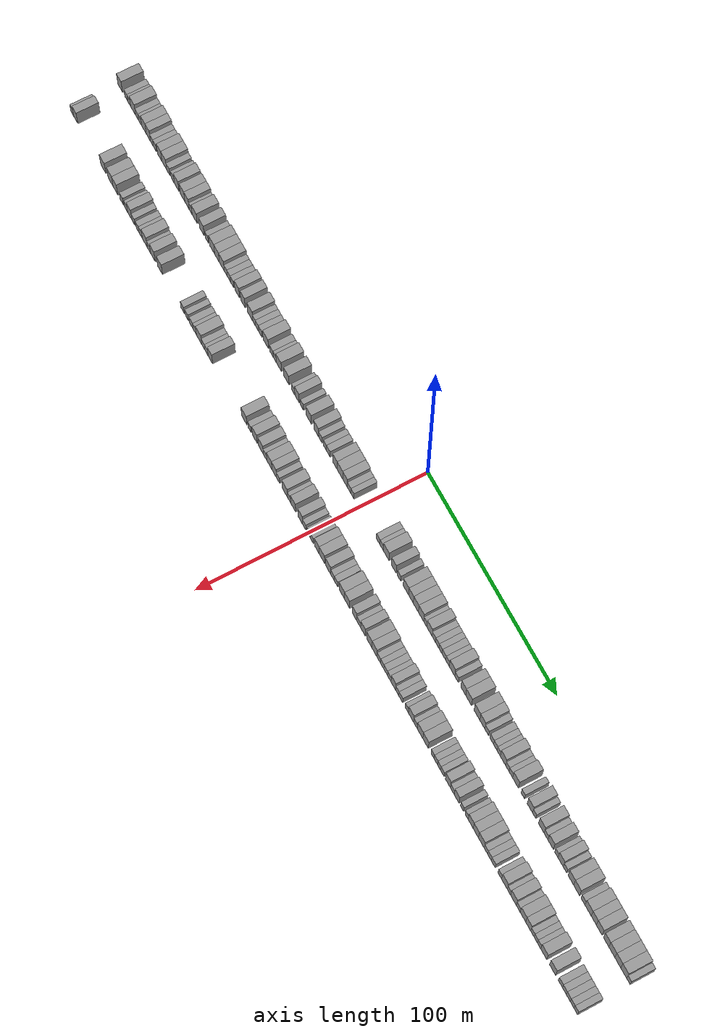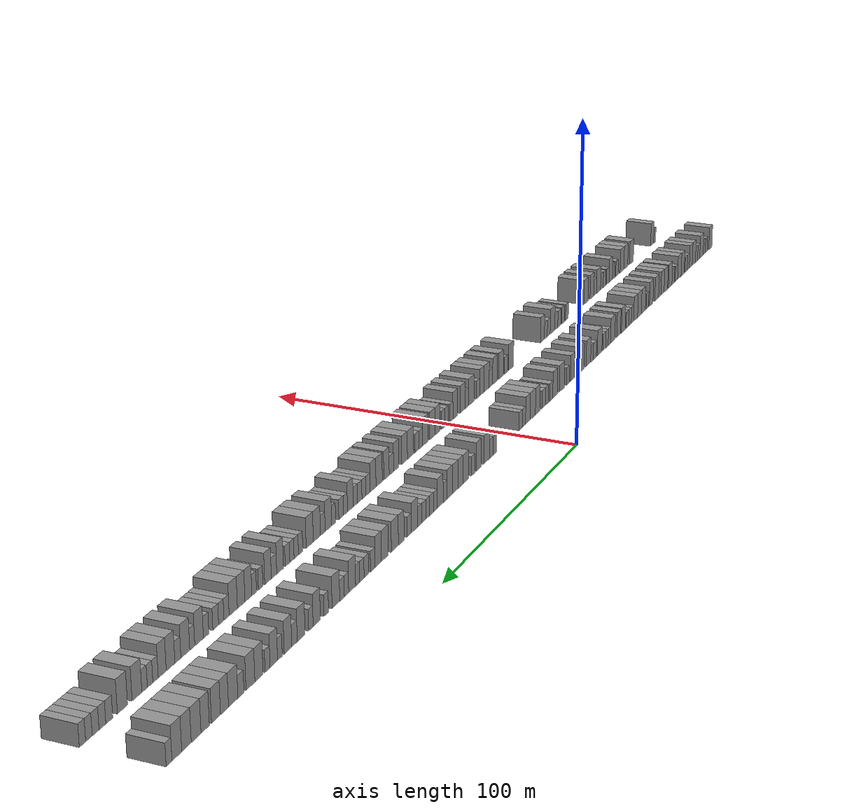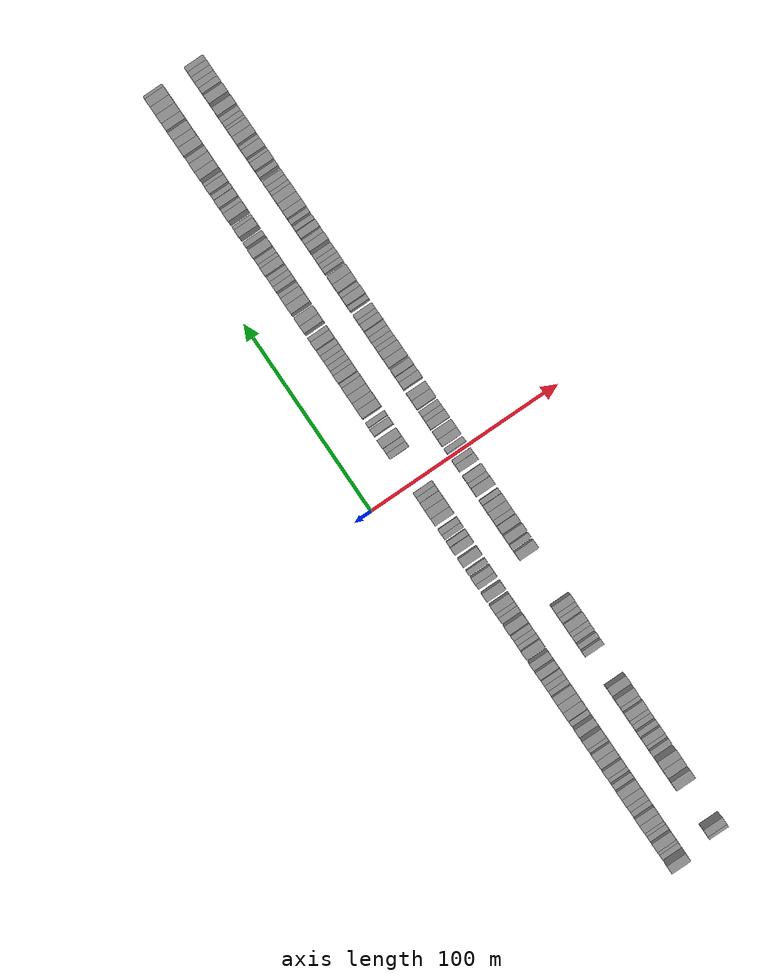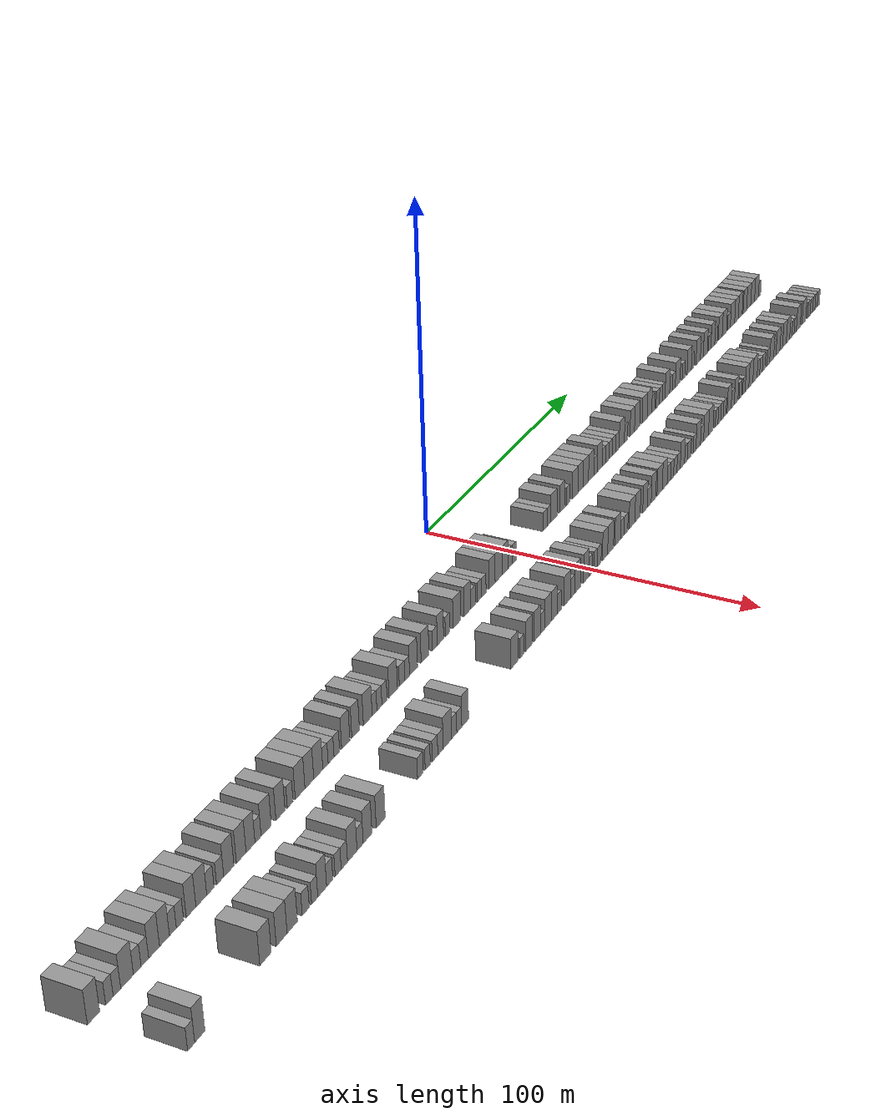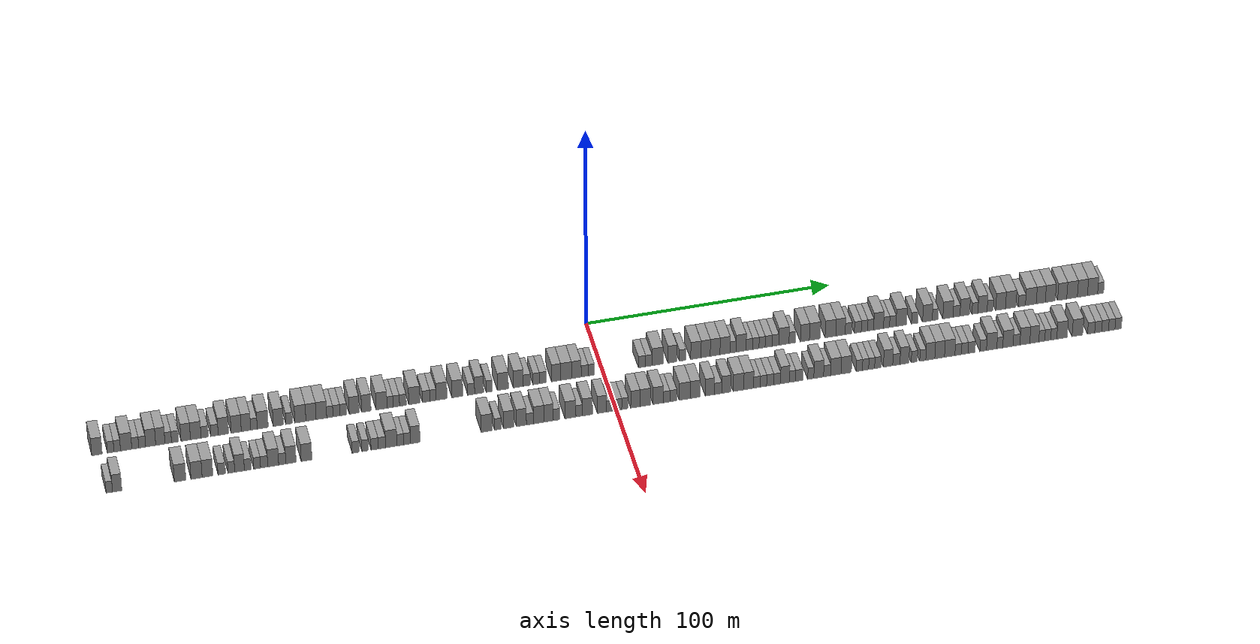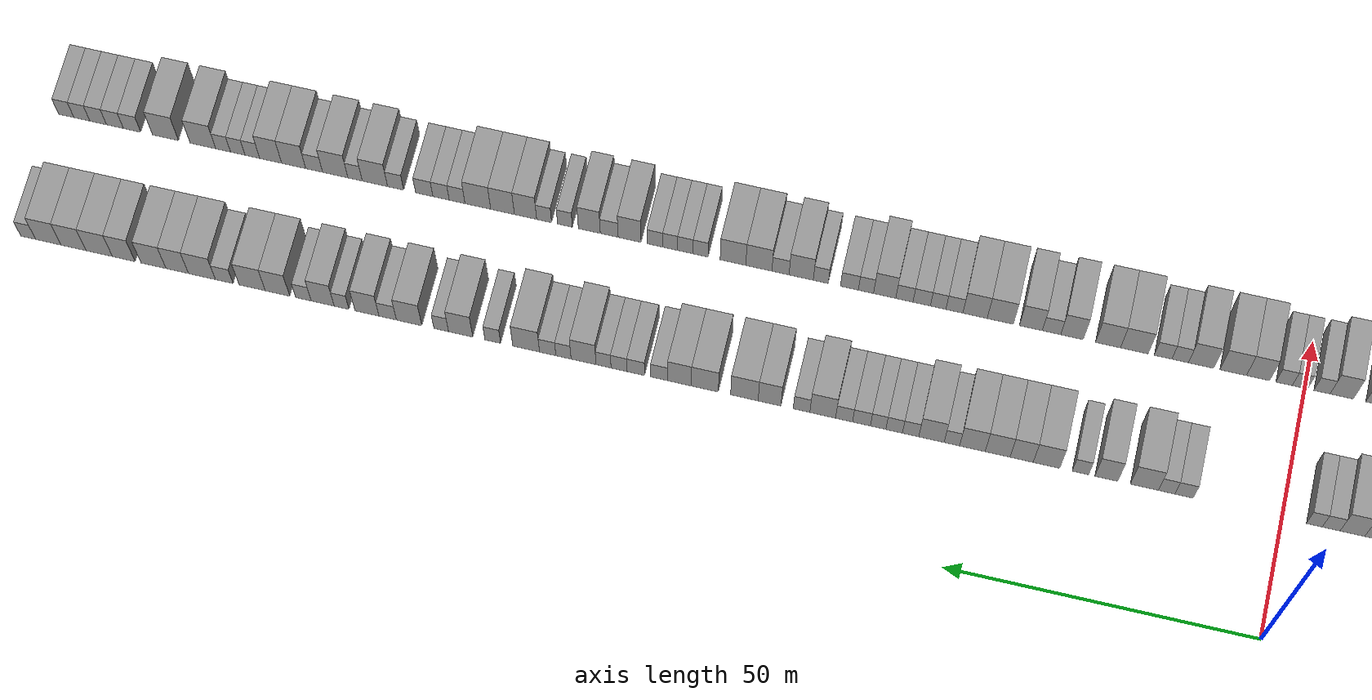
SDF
<sdf version="1.6">
 <world name="default">
  <scene>
   <sky><clouds><speed>12</speed></clouds></sky>
   <ambient>0.4 0.4 0.4 1</ambient>
   <background>0.7 0.7 0.7 1</background>
   <shadows>1</shadows>
  </scene>
  <gravity>0 0 -9.8066</gravity>
  <magnetic_field>6e-06 2.3e-05 -4.2e-05</magnetic_field>
  <physics default="0" name="default_physics" type="ode">
   <ode>
    <solver>
     <type>quick</type>
     <iters>10</iters>
     <sor>1.0</sor>
     <use_dynamic_moi_rescaling>0</use_dynamic_moi_rescaling>
    </solver>
    <constraints>
     <cfm>0</cfm>
     <erp>0.2</erp>
     <contact_max_correcting_vel>100</contact_max_correcting_vel>
     <contact_surface_layer>0.001</contact_surface_layer>
    </constraints>
   </ode>
   <max_step_size>0.004</max_step_size>
   <real_time_factor>1</real_time_factor>
   <real_time_update_rate>250</real_time_update_rate>
  </physics>
  <light name="sun" type="directional">
   <pose>0 0 10 0 0 0</pose>
   <diffuse>0.8 0.8 0.8 1</diffuse>
   <specular>0.2 0.2 0.2 1</specular>
   <attenuation>
    <range>1000</range>
    <constant>0.9</constant>
    <linear>0.01</linear>
    <quadratic>0.001</quadratic>
   </attenuation>
   <direction>-0.5 0.1 -0.9</direction>
  </light>
  <model name="building_1">
   <static>1</static>
   <pose>25.0000 -201.9423 0 0.000000 0.000000 0.000000</pose>
   <link name="link">
    <pose>0 0 4.50 0 0 0</pose>
    <collision name="collision"><geometry><box><size>10.0000 4.1153 9.0000</size></box></geometry></collision>
    <visual name="visual">
     <cast_shadows>0</cast_shadows>
     <geometry><box><size>10.0000 4.1153 9.0000</size></box></geometry>
     <material>
      <script>
       <uri>model://grey_wall/materials/scripts</uri>
       <uri>model://grey_wall/materials/textures</uri>
       <name>vrc/grey_wall</name>
      </script>
     </material>
    </visual>
   </link>
  </model>
  <model name="building_2">
   <static>1</static>
   <pose>25.0000 -196.5770 0 0.000000 0.000000 0.000000</pose>
   <link name="link">
    <pose>0 0 3.00 0 0 0</pose>
    <collision name="collision"><geometry><box><size>10.0000 2.6154 6.0000</size></box></geometry></collision>
    <visual name="visual">
     <cast_shadows>0</cast_shadows>
     <geometry><box><size>10.0000 2.6154 6.0000</size></box></geometry>
     <material>
      <script>
       <uri>model://grey_wall/materials/scripts</uri>
       <uri>model://grey_wall/materials/textures</uri>
       <name>vrc/grey_wall</name>
      </script>
     </material>
    </visual>
   </link>
  </model>
  <model name="building_3">
   <static>1</static>
   <pose>25.0000 -193.9902 0 0.000000 0.000000 0.000000</pose>
   <link name="link">
    <pose>0 0 3.00 0 0 0</pose>
    <collision name="collision"><geometry><box><size>10.0000 2.5582 6.0000</size></box></geometry></collision>
    <visual name="visual">
     <cast_shadows>0</cast_shadows>
     <geometry><box><size>10.0000 2.5582 6.0000</size></box></geometry>
     <material>
      <script>
       <uri>model://grey_wall/materials/scripts</uri>
       <uri>model://grey_wall/materials/textures</uri>
       <name>vrc/grey_wall</name>
      </script>
     </material>
    </visual>
   </link>
  </model>
  <model name="building_4">
   <static>1</static>
   <pose>25.0000 -190.4837 0 0.000000 0.000000 0.000000</pose>
   <link name="link">
    <pose>0 0 4.50 0 0 0</pose>
    <collision name="collision"><geometry><box><size>10.0000 4.4548 9.0000</size></box></geometry></collision>
    <visual name="visual">
     <cast_shadows>0</cast_shadows>
     <geometry><box><size>10.0000 4.4548 9.0000</size></box></geometry>
     <material>
      <script>
       <uri>model://grey_wall/materials/scripts</uri>
       <uri>model://grey_wall/materials/textures</uri>
       <name>vrc/grey_wall</name>
      </script>
     </material>
    </visual>
   </link>
  </model>
  <model name="building_5">
   <static>1</static>
   <pose>25.0000 -186.8945 0 0.000000 0.000000 0.000000</pose>
   <link name="link">
    <pose>0 0 3.00 0 0 0</pose>
    <collision name="collision"><geometry><box><size>10.0000 2.7236 6.0000</size></box></geometry></collision>
    <visual name="visual">
     <cast_shadows>0</cast_shadows>
     <geometry><box><size>10.0000 2.7236 6.0000</size></box></geometry>
     <material>
      <script>
       <uri>model://grey_wall/materials/scripts</uri>
       <uri>model://grey_wall/materials/textures</uri>
       <name>vrc/grey_wall</name>
      </script>
     </material>
    </visual>
   </link>
  </model>
  <model name="building_6">
   <static>1</static>
   <pose>25.0000 -184.1751 0 0.000000 0.000000 0.000000</pose>
   <link name="link">
    <pose>0 0 3.00 0 0 0</pose>
    <collision name="collision"><geometry><box><size>10.0000 2.7152 6.0000</size></box></geometry></collision>
    <visual name="visual">
     <cast_shadows>0</cast_shadows>
     <geometry><box><size>10.0000 2.7152 6.0000</size></box></geometry>
     <material>
      <script>
       <uri>model://grey_wall/materials/scripts</uri>
       <uri>model://grey_wall/materials/textures</uri>
       <name>vrc/grey_wall</name>
      </script>
     </material>
    </visual>
   </link>
  </model>
  <model name="building_7">
   <static>1</static>
   <pose>25.0000 -180.8436 0 0.000000 0.000000 0.000000</pose>
   <link name="link">
    <pose>0 0 4.50 0 0 0</pose>
    <collision name="collision"><geometry><box><size>10.0000 3.9480 9.0000</size></box></geometry></collision>
    <visual name="visual">
     <cast_shadows>0</cast_shadows>
     <geometry><box><size>10.0000 3.9480 9.0000</size></box></geometry>
     <material>
      <script>
       <uri>model://grey_wall/materials/scripts</uri>
       <uri>model://grey_wall/materials/textures</uri>
       <name>vrc/grey_wall</name>
      </script>
     </material>
    </visual>
   </link>
  </model>
  <model name="building_8">
   <static>1</static>
   <pose>25.0000 -177.0454 0 0.000000 0.000000 0.000000</pose>
   <link name="link">
    <pose>0 0 4.50 0 0 0</pose>
    <collision name="collision"><geometry><box><size>10.0000 3.6483 9.0000</size></box></geometry></collision>
    <visual name="visual">
     <cast_shadows>0</cast_shadows>
     <geometry><box><size>10.0000 3.6483 9.0000</size></box></geometry>
     <material>
      <script>
       <uri>model://grey_wall/materials/scripts</uri>
       <uri>model://grey_wall/materials/textures</uri>
       <name>vrc/grey_wall</name>
      </script>
     </material>
    </visual>
   </link>
  </model>
  <model name="building_9">
   <static>1</static>
   <pose>25.0000 -173.9322 0 0.000000 0.000000 0.000000</pose>
   <link name="link">
    <pose>0 0 3.00 0 0 0</pose>
    <collision name="collision"><geometry><box><size>10.0000 2.5782 6.0000</size></box></geometry></collision>
    <visual name="visual">
     <cast_shadows>0</cast_shadows>
     <geometry><box><size>10.0000 2.5782 6.0000</size></box></geometry>
     <material>
      <script>
       <uri>model://grey_wall/materials/scripts</uri>
       <uri>model://grey_wall/materials/textures</uri>
       <name>vrc/grey_wall</name>
      </script>
     </material>
    </visual>
   </link>
  </model>
  <model name="building_10">
   <static>1</static>
   <pose>25.0000 -171.2739 0 0.000000 0.000000 0.000000</pose>
   <link name="link">
    <pose>0 0 3.00 0 0 0</pose>
    <collision name="collision"><geometry><box><size>10.0000 2.7384 6.0000</size></box></geometry></collision>
    <visual name="visual">
     <cast_shadows>0</cast_shadows>
     <geometry><box><size>10.0000 2.7384 6.0000</size></box></geometry>
     <material>
      <script>
       <uri>model://grey_wall/materials/scripts</uri>
       <uri>model://grey_wall/materials/textures</uri>
       <name>vrc/grey_wall</name>
      </script>
     </material>
    </visual>
   </link>
  </model>
  <model name="building_11">
   <static>1</static>
   <pose>25.0000 -167.0471 0 0.000000 0.000000 0.000000</pose>
   <link name="link">
    <pose>0 0 4.50 0 0 0</pose>
    <collision name="collision"><geometry><box><size>10.0000 3.7153 9.0000</size></box></geometry></collision>
    <visual name="visual">
     <cast_shadows>0</cast_shadows>
     <geometry><box><size>10.0000 3.7153 9.0000</size></box></geometry>
     <material>
      <script>
       <uri>model://grey_wall/materials/scripts</uri>
       <uri>model://grey_wall/materials/textures</uri>
       <name>vrc/grey_wall</name>
      </script>
     </material>
    </visual>
   </link>
  </model>
  <model name="building_12">
   <static>1</static>
   <pose>25.0000 -163.0891 0 0.000000 0.000000 0.000000</pose>
   <link name="link">
    <pose>0 0 4.50 0 0 0</pose>
    <collision name="collision"><geometry><box><size>10.0000 4.2007 9.0000</size></box></geometry></collision>
    <visual name="visual">
     <cast_shadows>0</cast_shadows>
     <geometry><box><size>10.0000 4.2007 9.0000</size></box></geometry>
     <material>
      <script>
       <uri>model://grey_wall/materials/scripts</uri>
       <uri>model://grey_wall/materials/textures</uri>
       <name>vrc/grey_wall</name>
      </script>
     </material>
    </visual>
   </link>
  </model>
  <model name="building_13">
   <static>1</static>
   <pose>25.0000 -159.5519 0 0.000000 0.000000 0.000000</pose>
   <link name="link">
    <pose>0 0 3.00 0 0 0</pose>
    <collision name="collision"><geometry><box><size>10.0000 2.8738 6.0000</size></box></geometry></collision>
    <visual name="visual">
     <cast_shadows>0</cast_shadows>
     <geometry><box><size>10.0000 2.8738 6.0000</size></box></geometry>
     <material>
      <script>
       <uri>model://grey_wall/materials/scripts</uri>
       <uri>model://grey_wall/materials/textures</uri>
       <name>vrc/grey_wall</name>
      </script>
     </material>
    </visual>
   </link>
  </model>
  <model name="building_14">
   <static>1</static>
   <pose>25.0000 -155.6777 0 0.000000 0.000000 0.000000</pose>
   <link name="link">
    <pose>0 0 3.00 0 0 0</pose>
    <collision name="collision"><geometry><box><size>10.0000 2.8745 6.0000</size></box></geometry></collision>
    <visual name="visual">
     <cast_shadows>0</cast_shadows>
     <geometry><box><size>10.0000 2.8745 6.0000</size></box></geometry>
     <material>
      <script>
       <uri>model://grey_wall/materials/scripts</uri>
       <uri>model://grey_wall/materials/textures</uri>
       <name>vrc/grey_wall</name>
      </script>
     </material>
    </visual>
   </link>
  </model>
  <model name="building_15">
   <static>1</static>
   <pose>25.0000 -152.1802 0 0.000000 0.000000 0.000000</pose>
   <link name="link">
    <pose>0 0 4.50 0 0 0</pose>
    <collision name="collision"><geometry><box><size>10.0000 4.1206 9.0000</size></box></geometry></collision>
    <visual name="visual">
     <cast_shadows>0</cast_shadows>
     <geometry><box><size>10.0000 4.1206 9.0000</size></box></geometry>
     <material>
      <script>
       <uri>model://grey_wall/materials/scripts</uri>
       <uri>model://grey_wall/materials/textures</uri>
       <name>vrc/grey_wall</name>
      </script>
     </material>
    </visual>
   </link>
  </model>
  <model name="building_16">
   <static>1</static>
   <pose>25.0000 -147.1209 0 0.000000 0.000000 0.000000</pose>
   <link name="link">
    <pose>0 0 4.50 0 0 0</pose>
    <collision name="collision"><geometry><box><size>10.0000 3.9980 9.0000</size></box></geometry></collision>
    <visual name="visual">
     <cast_shadows>0</cast_shadows>
     <geometry><box><size>10.0000 3.9980 9.0000</size></box></geometry>
     <material>
      <script>
       <uri>model://grey_wall/materials/scripts</uri>
       <uri>model://grey_wall/materials/textures</uri>
       <name>vrc/grey_wall</name>
      </script>
     </material>
    </visual>
   </link>
  </model>
  <model name="building_17">
   <static>1</static>
   <pose>25.0000 -143.2498 0 0.000000 0.000000 0.000000</pose>
   <link name="link">
    <pose>0 0 4.50 0 0 0</pose>
    <collision name="collision"><geometry><box><size>10.0000 3.7441 9.0000</size></box></geometry></collision>
    <visual name="visual">
     <cast_shadows>0</cast_shadows>
     <geometry><box><size>10.0000 3.7441 9.0000</size></box></geometry>
     <material>
      <script>
       <uri>model://grey_wall/materials/scripts</uri>
       <uri>model://grey_wall/materials/textures</uri>
       <name>vrc/grey_wall</name>
      </script>
     </material>
    </visual>
   </link>
  </model>
  <model name="building_18">
   <static>1</static>
   <pose>25.0000 -140.0889 0 0.000000 0.000000 0.000000</pose>
   <link name="link">
    <pose>0 0 3.00 0 0 0</pose>
    <collision name="collision"><geometry><box><size>10.0000 2.5777 6.0000</size></box></geometry></collision>
    <visual name="visual">
     <cast_shadows>0</cast_shadows>
     <geometry><box><size>10.0000 2.5777 6.0000</size></box></geometry>
     <material>
      <script>
       <uri>model://grey_wall/materials/scripts</uri>
       <uri>model://grey_wall/materials/textures</uri>
       <name>vrc/grey_wall</name>
      </script>
     </material>
    </visual>
   </link>
  </model>
  <model name="building_19">
   <static>1</static>
   <pose>25.0000 -136.6142 0 0.000000 0.000000 0.000000</pose>
   <link name="link">
    <pose>0 0 4.50 0 0 0</pose>
    <collision name="collision"><geometry><box><size>10.0000 4.3716 9.0000</size></box></geometry></collision>
    <visual name="visual">
     <cast_shadows>0</cast_shadows>
     <geometry><box><size>10.0000 4.3716 9.0000</size></box></geometry>
     <material>
      <script>
       <uri>model://grey_wall/materials/scripts</uri>
       <uri>model://grey_wall/materials/textures</uri>
       <name>vrc/grey_wall</name>
      </script>
     </material>
    </visual>
   </link>
  </model>
  <model name="building_20">
   <static>1</static>
   <pose>25.0000 -130.4317 0 0.000000 0.000000 0.000000</pose>
   <link name="link">
    <pose>0 0 4.50 0 0 0</pose>
    <collision name="collision"><geometry><box><size>10.0000 3.9935 9.0000</size></box></geometry></collision>
    <visual name="visual">
     <cast_shadows>0</cast_shadows>
     <geometry><box><size>10.0000 3.9935 9.0000</size></box></geometry>
     <material>
      <script>
       <uri>model://grey_wall/materials/scripts</uri>
       <uri>model://grey_wall/materials/textures</uri>
       <name>vrc/grey_wall</name>
      </script>
     </material>
    </visual>
   </link>
  </model>
  <model name="building_21">
   <static>1</static>
   <pose>25.0000 -126.1475 0 0.000000 0.000000 0.000000</pose>
   <link name="link">
    <pose>0 0 3.00 0 0 0</pose>
    <collision name="collision"><geometry><box><size>10.0000 2.5748 6.0000</size></box></geometry></collision>
    <visual name="visual">
     <cast_shadows>0</cast_shadows>
     <geometry><box><size>10.0000 2.5748 6.0000</size></box></geometry>
     <material>
      <script>
       <uri>model://grey_wall/materials/scripts</uri>
       <uri>model://grey_wall/materials/textures</uri>
       <name>vrc/grey_wall</name>
      </script>
     </material>
    </visual>
   </link>
  </model>
  <model name="building_22">
   <static>1</static>
   <pose>25.0000 -121.6800 0 0.000000 0.000000 0.000000</pose>
   <link name="link">
    <pose>0 0 4.50 0 0 0</pose>
    <collision name="collision"><geometry><box><size>10.0000 4.3604 9.0000</size></box></geometry></collision>
    <visual name="visual">
     <cast_shadows>0</cast_shadows>
     <geometry><box><size>10.0000 4.3604 9.0000</size></box></geometry>
     <material>
      <script>
       <uri>model://grey_wall/materials/scripts</uri>
       <uri>model://grey_wall/materials/textures</uri>
       <name>vrc/grey_wall</name>
      </script>
     </material>
    </visual>
   </link>
  </model>
  <model name="building_23">
   <static>1</static>
   <pose>25.0000 -117.4718 0 0.000000 0.000000 0.000000</pose>
   <link name="link">
    <pose>0 0 4.50 0 0 0</pose>
    <collision name="collision"><geometry><box><size>10.0000 4.0561 9.0000</size></box></geometry></collision>
    <visual name="visual">
     <cast_shadows>0</cast_shadows>
     <geometry><box><size>10.0000 4.0561 9.0000</size></box></geometry>
     <material>
      <script>
       <uri>model://grey_wall/materials/scripts</uri>
       <uri>model://grey_wall/materials/textures</uri>
       <name>vrc/grey_wall</name>
      </script>
     </material>
    </visual>
   </link>
  </model>
  <model name="building_24">
   <static>1</static>
   <pose>25.0000 -113.3345 0 0.000000 0.000000 0.000000</pose>
   <link name="link">
    <pose>0 0 4.50 0 0 0</pose>
    <collision name="collision"><geometry><box><size>10.0000 4.2184 9.0000</size></box></geometry></collision>
    <visual name="visual">
     <cast_shadows>0</cast_shadows>
     <geometry><box><size>10.0000 4.2184 9.0000</size></box></geometry>
     <material>
      <script>
       <uri>model://grey_wall/materials/scripts</uri>
       <uri>model://grey_wall/materials/textures</uri>
       <name>vrc/grey_wall</name>
      </script>
     </material>
    </visual>
   </link>
  </model>
  <model name="building_25">
   <static>1</static>
   <pose>25.0000 -109.9702 0 0.000000 0.000000 0.000000</pose>
   <link name="link">
    <pose>0 0 3.00 0 0 0</pose>
    <collision name="collision"><geometry><box><size>10.0000 2.5103 6.0000</size></box></geometry></collision>
    <visual name="visual">
     <cast_shadows>0</cast_shadows>
     <geometry><box><size>10.0000 2.5103 6.0000</size></box></geometry>
     <material>
      <script>
       <uri>model://grey_wall/materials/scripts</uri>
       <uri>model://grey_wall/materials/textures</uri>
       <name>vrc/grey_wall</name>
      </script>
     </material>
    </visual>
   </link>
  </model>
  <model name="building_26">
   <static>1</static>
   <pose>25.0000 -107.3173 0 0.000000 0.000000 0.000000</pose>
   <link name="link">
    <pose>0 0 3.00 0 0 0</pose>
    <collision name="collision"><geometry><box><size>10.0000 2.7954 6.0000</size></box></geometry></collision>
    <visual name="visual">
     <cast_shadows>0</cast_shadows>
     <geometry><box><size>10.0000 2.7954 6.0000</size></box></geometry>
     <material>
      <script>
       <uri>model://grey_wall/materials/scripts</uri>
       <uri>model://grey_wall/materials/textures</uri>
       <name>vrc/grey_wall</name>
      </script>
     </material>
    </visual>
   </link>
  </model>
  <model name="building_27">
   <static>1</static>
   <pose>25.0000 -104.5881 0 0.000000 0.000000 0.000000</pose>
   <link name="link">
    <pose>0 0 3.00 0 0 0</pose>
    <collision name="collision"><geometry><box><size>10.0000 2.6630 6.0000</size></box></geometry></collision>
    <visual name="visual">
     <cast_shadows>0</cast_shadows>
     <geometry><box><size>10.0000 2.6630 6.0000</size></box></geometry>
     <material>
      <script>
       <uri>model://grey_wall/materials/scripts</uri>
       <uri>model://grey_wall/materials/textures</uri>
       <name>vrc/grey_wall</name>
      </script>
     </material>
    </visual>
   </link>
  </model>
  <model name="building_28">
   <static>1</static>
   <pose>25.0000 -100.2743 0 0.000000 0.000000 0.000000</pose>
   <link name="link">
    <pose>0 0 4.50 0 0 0</pose>
    <collision name="collision"><geometry><box><size>10.0000 3.9646 9.0000</size></box></geometry></collision>
    <visual name="visual">
     <cast_shadows>0</cast_shadows>
     <geometry><box><size>10.0000 3.9646 9.0000</size></box></geometry>
     <material>
      <script>
       <uri>model://grey_wall/materials/scripts</uri>
       <uri>model://grey_wall/materials/textures</uri>
       <name>vrc/grey_wall</name>
      </script>
     </material>
    </visual>
   </link>
  </model>
  <model name="building_29">
   <static>1</static>
   <pose>25.0000 -95.4262 0 0.000000 0.000000 0.000000</pose>
   <link name="link">
    <pose>0 0 4.50 0 0 0</pose>
    <collision name="collision"><geometry><box><size>10.0000 3.7315 9.0000</size></box></geometry></collision>
    <visual name="visual">
     <cast_shadows>0</cast_shadows>
     <geometry><box><size>10.0000 3.7315 9.0000</size></box></geometry>
     <material>
      <script>
       <uri>model://grey_wall/materials/scripts</uri>
       <uri>model://grey_wall/materials/textures</uri>
       <name>vrc/grey_wall</name>
      </script>
     </material>
    </visual>
   </link>
  </model>
  <model name="building_30">
   <static>1</static>
   <pose>25.0000 -89.3529 0 0.000000 0.000000 0.000000</pose>
   <link name="link">
    <pose>0 0 4.50 0 0 0</pose>
    <collision name="collision"><geometry><box><size>10.0000 4.4151 9.0000</size></box></geometry></collision>
    <visual name="visual">
     <cast_shadows>0</cast_shadows>
     <geometry><box><size>10.0000 4.4151 9.0000</size></box></geometry>
     <material>
      <script>
       <uri>model://grey_wall/materials/scripts</uri>
       <uri>model://grey_wall/materials/textures</uri>
       <name>vrc/grey_wall</name>
      </script>
     </material>
    </visual>
   </link>
  </model>
  <model name="building_31">
   <static>1</static>
   <pose>25.0000 -85.9377 0 0.000000 0.000000 0.000000</pose>
   <link name="link">
    <pose>0 0 3.00 0 0 0</pose>
    <collision name="collision"><geometry><box><size>10.0000 2.4154 6.0000</size></box></geometry></collision>
    <visual name="visual">
     <cast_shadows>0</cast_shadows>
     <geometry><box><size>10.0000 2.4154 6.0000</size></box></geometry>
     <material>
      <script>
       <uri>model://grey_wall/materials/scripts</uri>
       <uri>model://grey_wall/materials/textures</uri>
       <name>vrc/grey_wall</name>
      </script>
     </material>
    </visual>
   </link>
  </model>
  <model name="building_32">
   <static>1</static>
   <pose>25.0000 -83.4463 0 0.000000 0.000000 0.000000</pose>
   <link name="link">
    <pose>0 0 3.00 0 0 0</pose>
    <collision name="collision"><geometry><box><size>10.0000 2.5673 6.0000</size></box></geometry></collision>
    <visual name="visual">
     <cast_shadows>0</cast_shadows>
     <geometry><box><size>10.0000 2.5673 6.0000</size></box></geometry>
     <material>
      <script>
       <uri>model://grey_wall/materials/scripts</uri>
       <uri>model://grey_wall/materials/textures</uri>
       <name>vrc/grey_wall</name>
      </script>
     </material>
    </visual>
   </link>
  </model>
  <model name="building_33">
   <static>1</static>
   <pose>25.0000 -80.8120 0 0.000000 0.000000 0.000000</pose>
   <link name="link">
    <pose>0 0 3.00 0 0 0</pose>
    <collision name="collision"><geometry><box><size>10.0000 2.7014 6.0000</size></box></geometry></collision>
    <visual name="visual">
     <cast_shadows>0</cast_shadows>
     <geometry><box><size>10.0000 2.7014 6.0000</size></box></geometry>
     <material>
      <script>
       <uri>model://grey_wall/materials/scripts</uri>
       <uri>model://grey_wall/materials/textures</uri>
       <name>vrc/grey_wall</name>
      </script>
     </material>
    </visual>
   </link>
  </model>
  <model name="building_34">
   <static>1</static>
   <pose>25.0000 -76.2308 0 0.000000 0.000000 0.000000</pose>
   <link name="link">
    <pose>0 0 4.50 0 0 0</pose>
    <collision name="collision"><geometry><box><size>10.0000 4.4610 9.0000</size></box></geometry></collision>
    <visual name="visual">
     <cast_shadows>0</cast_shadows>
     <geometry><box><size>10.0000 4.4610 9.0000</size></box></geometry>
     <material>
      <script>
       <uri>model://grey_wall/materials/scripts</uri>
       <uri>model://grey_wall/materials/textures</uri>
       <name>vrc/grey_wall</name>
      </script>
     </material>
    </visual>
   </link>
  </model>
  <model name="building_35">
   <static>1</static>
   <pose>25.0000 -71.5075 0 0.000000 0.000000 0.000000</pose>
   <link name="link">
    <pose>0 0 3.00 0 0 0</pose>
    <collision name="collision"><geometry><box><size>10.0000 2.9858 6.0000</size></box></geometry></collision>
    <visual name="visual">
     <cast_shadows>0</cast_shadows>
     <geometry><box><size>10.0000 2.9858 6.0000</size></box></geometry>
     <material>
      <script>
       <uri>model://grey_wall/materials/scripts</uri>
       <uri>model://grey_wall/materials/textures</uri>
       <name>vrc/grey_wall</name>
      </script>
     </material>
    </visual>
   </link>
  </model>
  <model name="building_36">
   <static>1</static>
   <pose>25.0000 -68.7526 0 0.000000 0.000000 0.000000</pose>
   <link name="link">
    <pose>0 0 3.00 0 0 0</pose>
    <collision name="collision"><geometry><box><size>10.0000 2.5241 6.0000</size></box></geometry></collision>
    <visual name="visual">
     <cast_shadows>0</cast_shadows>
     <geometry><box><size>10.0000 2.5241 6.0000</size></box></geometry>
     <material>
      <script>
       <uri>model://grey_wall/materials/scripts</uri>
       <uri>model://grey_wall/materials/textures</uri>
       <name>vrc/grey_wall</name>
      </script>
     </material>
    </visual>
   </link>
  </model>
  <model name="building_37">
   <static>1</static>
   <pose>25.0000 -65.3271 0 0.000000 0.000000 0.000000</pose>
   <link name="link">
    <pose>0 0 4.50 0 0 0</pose>
    <collision name="collision"><geometry><box><size>10.0000 4.3268 9.0000</size></box></geometry></collision>
    <visual name="visual">
     <cast_shadows>0</cast_shadows>
     <geometry><box><size>10.0000 4.3268 9.0000</size></box></geometry>
     <material>
      <script>
       <uri>model://grey_wall/materials/scripts</uri>
       <uri>model://grey_wall/materials/textures</uri>
       <name>vrc/grey_wall</name>
      </script>
     </material>
    </visual>
   </link>
  </model>
  <model name="building_38">
   <static>1</static>
   <pose>25.0000 -58.9984 0 0.000000 0.000000 0.000000</pose>
   <link name="link">
    <pose>0 0 4.50 0 0 0</pose>
    <collision name="collision"><geometry><box><size>10.0000 4.3307 9.0000</size></box></geometry></collision>
    <visual name="visual">
     <cast_shadows>0</cast_shadows>
     <geometry><box><size>10.0000 4.3307 9.0000</size></box></geometry>
     <material>
      <script>
       <uri>model://grey_wall/materials/scripts</uri>
       <uri>model://grey_wall/materials/textures</uri>
       <name>vrc/grey_wall</name>
      </script>
     </material>
    </visual>
   </link>
  </model>
  <model name="building_39">
   <static>1</static>
   <pose>25.0000 -53.4522 0 0.000000 0.000000 0.000000</pose>
   <link name="link">
    <pose>0 0 3.00 0 0 0</pose>
    <collision name="collision"><geometry><box><size>10.0000 2.7616 6.0000</size></box></geometry></collision>
    <visual name="visual">
     <cast_shadows>0</cast_shadows>
     <geometry><box><size>10.0000 2.7616 6.0000</size></box></geometry>
     <material>
      <script>
       <uri>model://grey_wall/materials/scripts</uri>
       <uri>model://grey_wall/materials/textures</uri>
       <name>vrc/grey_wall</name>
      </script>
     </material>
    </visual>
   </link>
  </model>
  <model name="building_40">
   <static>1</static>
   <pose>25.0000 -50.2697 0 0.000000 0.000000 0.000000</pose>
   <link name="link">
    <pose>0 0 4.50 0 0 0</pose>
    <collision name="collision"><geometry><box><size>10.0000 3.6035 9.0000</size></box></geometry></collision>
    <visual name="visual">
     <cast_shadows>0</cast_shadows>
     <geometry><box><size>10.0000 3.6035 9.0000</size></box></geometry>
     <material>
      <script>
       <uri>model://grey_wall/materials/scripts</uri>
       <uri>model://grey_wall/materials/textures</uri>
       <name>vrc/grey_wall</name>
      </script>
     </material>
    </visual>
   </link>
  </model>
  <model name="building_41">
   <static>1</static>
   <pose>25.0000 -46.1972 0 0.000000 0.000000 0.000000</pose>
   <link name="link">
    <pose>0 0 3.00 0 0 0</pose>
    <collision name="collision"><geometry><box><size>10.0000 2.5414 6.0000</size></box></geometry></collision>
    <visual name="visual">
     <cast_shadows>0</cast_shadows>
     <geometry><box><size>10.0000 2.5414 6.0000</size></box></geometry>
     <material>
      <script>
       <uri>model://grey_wall/materials/scripts</uri>
       <uri>model://grey_wall/materials/textures</uri>
       <name>vrc/grey_wall</name>
      </script>
     </material>
    </visual>
   </link>
  </model>
  <model name="building_42">
   <static>1</static>
   <pose>25.0000 -40.7090 0 0.000000 0.000000 0.000000</pose>
   <link name="link">
    <pose>0 0 4.50 0 0 0</pose>
    <collision name="collision"><geometry><box><size>10.0000 4.4350 9.0000</size></box></geometry></collision>
    <visual name="visual">
     <cast_shadows>0</cast_shadows>
     <geometry><box><size>10.0000 4.4350 9.0000</size></box></geometry>
     <material>
      <script>
       <uri>model://grey_wall/materials/scripts</uri>
       <uri>model://grey_wall/materials/textures</uri>
       <name>vrc/grey_wall</name>
      </script>
     </material>
    </visual>
   </link>
  </model>
  <model name="building_43">
   <static>1</static>
   <pose>25.0000 -34.4842 0 0.000000 0.000000 0.000000</pose>
   <link name="link">
    <pose>0 0 4.50 0 0 0</pose>
    <collision name="collision"><geometry><box><size>10.0000 4.0146 9.0000</size></box></geometry></collision>
    <visual name="visual">
     <cast_shadows>0</cast_shadows>
     <geometry><box><size>10.0000 4.0146 9.0000</size></box></geometry>
     <material>
      <script>
       <uri>model://grey_wall/materials/scripts</uri>
       <uri>model://grey_wall/materials/textures</uri>
       <name>vrc/grey_wall</name>
      </script>
     </material>
    </visual>
   </link>
  </model>
  <model name="building_44">
   <static>1</static>
   <pose>25.0000 -31.0404 0 0.000000 0.000000 0.000000</pose>
   <link name="link">
    <pose>0 0 3.00 0 0 0</pose>
    <collision name="collision"><geometry><box><size>10.0000 2.8728 6.0000</size></box></geometry></collision>
    <visual name="visual">
     <cast_shadows>0</cast_shadows>
     <geometry><box><size>10.0000 2.8728 6.0000</size></box></geometry>
     <material>
      <script>
       <uri>model://grey_wall/materials/scripts</uri>
       <uri>model://grey_wall/materials/textures</uri>
       <name>vrc/grey_wall</name>
      </script>
     </material>
    </visual>
   </link>
  </model>
  <model name="building_45">
   <static>1</static>
   <pose>25.0000 -27.3285 0 0.000000 0.000000 0.000000</pose>
   <link name="link">
    <pose>0 0 3.00 0 0 0</pose>
    <collision name="collision"><geometry><box><size>10.0000 2.5510 6.0000</size></box></geometry></collision>
    <visual name="visual">
     <cast_shadows>0</cast_shadows>
     <geometry><box><size>10.0000 2.5510 6.0000</size></box></geometry>
     <material>
      <script>
       <uri>model://grey_wall/materials/scripts</uri>
       <uri>model://grey_wall/materials/textures</uri>
       <name>vrc/grey_wall</name>
      </script>
     </material>
    </visual>
   </link>
  </model>
  <model name="building_46">
   <static>1</static>
   <pose>25.0000 -24.5753 0 0.000000 0.000000 0.000000</pose>
   <link name="link">
    <pose>0 0 3.00 0 0 0</pose>
    <collision name="collision"><geometry><box><size>10.0000 2.9554 6.0000</size></box></geometry></collision>
    <visual name="visual">
     <cast_shadows>0</cast_shadows>
     <geometry><box><size>10.0000 2.9554 6.0000</size></box></geometry>
     <material>
      <script>
       <uri>model://grey_wall/materials/scripts</uri>
       <uri>model://grey_wall/materials/textures</uri>
       <name>vrc/grey_wall</name>
      </script>
     </material>
    </visual>
   </link>
  </model>
  <model name="building_47">
   <static>1</static>
   <pose>25.0000 -19.2505 0 0.000000 0.000000 0.000000</pose>
   <link name="link">
    <pose>0 0 4.50 0 0 0</pose>
    <collision name="collision"><geometry><box><size>10.0000 3.6943 9.0000</size></box></geometry></collision>
    <visual name="visual">
     <cast_shadows>0</cast_shadows>
     <geometry><box><size>10.0000 3.6943 9.0000</size></box></geometry>
     <material>
      <script>
       <uri>model://grey_wall/materials/scripts</uri>
       <uri>model://grey_wall/materials/textures</uri>
       <name>vrc/grey_wall</name>
      </script>
     </material>
    </visual>
   </link>
  </model>
  <model name="building_48">
   <static>1</static>
   <pose>25.0000 -15.1972 0 0.000000 0.000000 0.000000</pose>
   <link name="link">
    <pose>0 0 4.50 0 0 0</pose>
    <collision name="collision"><geometry><box><size>10.0000 4.4121 9.0000</size></box></geometry></collision>
    <visual name="visual">
     <cast_shadows>0</cast_shadows>
     <geometry><box><size>10.0000 4.4121 9.0000</size></box></geometry>
     <material>
      <script>
       <uri>model://grey_wall/materials/scripts</uri>
       <uri>model://grey_wall/materials/textures</uri>
       <name>vrc/grey_wall</name>
      </script>
     </material>
    </visual>
   </link>
  </model>
  <model name="building_49">
   <static>1</static>
   <pose>25.0000 -11.0496 0 0.000000 0.000000 0.000000</pose>
   <link name="link">
    <pose>0 0 4.50 0 0 0</pose>
    <collision name="collision"><geometry><box><size>10.0000 3.8831 9.0000</size></box></geometry></collision>
    <visual name="visual">
     <cast_shadows>0</cast_shadows>
     <geometry><box><size>10.0000 3.8831 9.0000</size></box></geometry>
     <material>
      <script>
       <uri>model://grey_wall/materials/scripts</uri>
       <uri>model://grey_wall/materials/textures</uri>
       <name>vrc/grey_wall</name>
      </script>
     </material>
    </visual>
   </link>
  </model>
  <model name="building_50">
   <static>1</static>
   <pose>25.0000 -7.7061 0 0.000000 0.000000 0.000000</pose>
   <link name="link">
    <pose>0 0 3.00 0 0 0</pose>
    <collision name="collision"><geometry><box><size>10.0000 2.8038 6.0000</size></box></geometry></collision>
    <visual name="visual">
     <cast_shadows>0</cast_shadows>
     <geometry><box><size>10.0000 2.8038 6.0000</size></box></geometry>
     <material>
      <script>
       <uri>model://grey_wall/materials/scripts</uri>
       <uri>model://grey_wall/materials/textures</uri>
       <name>vrc/grey_wall</name>
      </script>
     </material>
    </visual>
   </link>
  </model>
  <model name="building_51">
   <static>1</static>
   <pose>25.0000 -5.0564 0 0.000000 0.000000 0.000000</pose>
   <link name="link">
    <pose>0 0 3.00 0 0 0</pose>
    <collision name="collision"><geometry><box><size>10.0000 2.4957 6.0000</size></box></geometry></collision>
    <visual name="visual">
     <cast_shadows>0</cast_shadows>
     <geometry><box><size>10.0000 2.4957 6.0000</size></box></geometry>
     <material>
      <script>
       <uri>model://grey_wall/materials/scripts</uri>
       <uri>model://grey_wall/materials/textures</uri>
       <name>vrc/grey_wall</name>
      </script>
     </material>
    </visual>
   </link>
  </model>
  <model name="building_52">
   <static>1</static>
   <pose>25.0000 15.5653 0 0.000000 0.000000 0.000000</pose>
   <link name="link">
    <pose>0 0 3.00 0 0 0</pose>
    <collision name="collision"><geometry><box><size>10.0000 2.9159 6.0000</size></box></geometry></collision>
    <visual name="visual">
     <cast_shadows>0</cast_shadows>
     <geometry><box><size>10.0000 2.9159 6.0000</size></box></geometry>
     <material>
      <script>
       <uri>model://grey_wall/materials/scripts</uri>
       <uri>model://grey_wall/materials/textures</uri>
       <name>vrc/grey_wall</name>
      </script>
     </material>
    </visual>
   </link>
  </model>
  <model name="building_53">
   <static>1</static>
   <pose>25.0000 18.3170 0 0.000000 0.000000 0.000000</pose>
   <link name="link">
    <pose>0 0 3.00 0 0 0</pose>
    <collision name="collision"><geometry><box><size>10.0000 2.5877 6.0000</size></box></geometry></collision>
    <visual name="visual">
     <cast_shadows>0</cast_shadows>
     <geometry><box><size>10.0000 2.5877 6.0000</size></box></geometry>
     <material>
      <script>
       <uri>model://grey_wall/materials/scripts</uri>
       <uri>model://grey_wall/materials/textures</uri>
       <name>vrc/grey_wall</name>
      </script>
     </material>
    </visual>
   </link>
  </model>
  <model name="building_54">
   <static>1</static>
   <pose>25.0000 21.8488 0 0.000000 0.000000 0.000000</pose>
   <link name="link">
    <pose>0 0 4.50 0 0 0</pose>
    <collision name="collision"><geometry><box><size>10.0000 4.4759 9.0000</size></box></geometry></collision>
    <visual name="visual">
     <cast_shadows>0</cast_shadows>
     <geometry><box><size>10.0000 4.4759 9.0000</size></box></geometry>
     <material>
      <script>
       <uri>model://grey_wall/materials/scripts</uri>
       <uri>model://grey_wall/materials/textures</uri>
       <name>vrc/grey_wall</name>
      </script>
     </material>
    </visual>
   </link>
  </model>
  <model name="building_55">
   <static>1</static>
   <pose>25.0000 27.9131 0 0.000000 0.000000 0.000000</pose>
   <link name="link">
    <pose>0 0 4.50 0 0 0</pose>
    <collision name="collision"><geometry><box><size>10.0000 3.6527 9.0000</size></box></geometry></collision>
    <visual name="visual">
     <cast_shadows>0</cast_shadows>
     <geometry><box><size>10.0000 3.6527 9.0000</size></box></geometry>
     <material>
      <script>
       <uri>model://grey_wall/materials/scripts</uri>
       <uri>model://grey_wall/materials/textures</uri>
       <name>vrc/grey_wall</name>
      </script>
     </material>
    </visual>
   </link>
  </model>
  <model name="building_56">
   <static>1</static>
   <pose>25.0000 32.0451 0 0.000000 0.000000 0.000000</pose>
   <link name="link">
    <pose>0 0 3.00 0 0 0</pose>
    <collision name="collision"><geometry><box><size>10.0000 2.6112 6.0000</size></box></geometry></collision>
    <visual name="visual">
     <cast_shadows>0</cast_shadows>
     <geometry><box><size>10.0000 2.6112 6.0000</size></box></geometry>
     <material>
      <script>
       <uri>model://grey_wall/materials/scripts</uri>
       <uri>model://grey_wall/materials/textures</uri>
       <name>vrc/grey_wall</name>
      </script>
     </material>
    </visual>
   </link>
  </model>
  <model name="building_57">
   <static>1</static>
   <pose>25.0000 37.4714 0 0.000000 0.000000 0.000000</pose>
   <link name="link">
    <pose>0 0 4.50 0 0 0</pose>
    <collision name="collision"><geometry><box><size>10.0000 4.2415 9.0000</size></box></geometry></collision>
    <visual name="visual">
     <cast_shadows>0</cast_shadows>
     <geometry><box><size>10.0000 4.2415 9.0000</size></box></geometry>
     <material>
      <script>
       <uri>model://grey_wall/materials/scripts</uri>
       <uri>model://grey_wall/materials/textures</uri>
       <name>vrc/grey_wall</name>
      </script>
     </material>
    </visual>
   </link>
  </model>
  <model name="building_58">
   <static>1</static>
   <pose>25.0000 41.4529 0 0.000000 0.000000 0.000000</pose>
   <link name="link">
    <pose>0 0 4.50 0 0 0</pose>
    <collision name="collision"><geometry><box><size>10.0000 3.7214 9.0000</size></box></geometry></collision>
    <visual name="visual">
     <cast_shadows>0</cast_shadows>
     <geometry><box><size>10.0000 3.7214 9.0000</size></box></geometry>
     <material>
      <script>
       <uri>model://grey_wall/materials/scripts</uri>
       <uri>model://grey_wall/materials/textures</uri>
       <name>vrc/grey_wall</name>
      </script>
     </material>
    </visual>
   </link>
  </model>
  <model name="building_59">
   <static>1</static>
   <pose>25.0000 45.3034 0 0.000000 0.000000 0.000000</pose>
   <link name="link">
    <pose>0 0 4.50 0 0 0</pose>
    <collision name="collision"><geometry><box><size>10.0000 3.9796 9.0000</size></box></geometry></collision>
    <visual name="visual">
     <cast_shadows>0</cast_shadows>
     <geometry><box><size>10.0000 3.9796 9.0000</size></box></geometry>
     <material>
      <script>
       <uri>model://grey_wall/materials/scripts</uri>
       <uri>model://grey_wall/materials/textures</uri>
       <name>vrc/grey_wall</name>
      </script>
     </material>
    </visual>
   </link>
  </model>
  <model name="building_60">
   <static>1</static>
   <pose>25.0000 49.3481 0 0.000000 0.000000 0.000000</pose>
   <link name="link">
    <pose>0 0 4.50 0 0 0</pose>
    <collision name="collision"><geometry><box><size>10.0000 4.1098 9.0000</size></box></geometry></collision>
    <visual name="visual">
     <cast_shadows>0</cast_shadows>
     <geometry><box><size>10.0000 4.1098 9.0000</size></box></geometry>
     <material>
      <script>
       <uri>model://grey_wall/materials/scripts</uri>
       <uri>model://grey_wall/materials/textures</uri>
       <name>vrc/grey_wall</name>
      </script>
     </material>
    </visual>
   </link>
  </model>
  <model name="building_61">
   <static>1</static>
   <pose>25.0000 52.6448 0 0.000000 0.000000 0.000000</pose>
   <link name="link">
    <pose>0 0 3.00 0 0 0</pose>
    <collision name="collision"><geometry><box><size>10.0000 2.4836 6.0000</size></box></geometry></collision>
    <visual name="visual">
     <cast_shadows>0</cast_shadows>
     <geometry><box><size>10.0000 2.4836 6.0000</size></box></geometry>
     <material>
      <script>
       <uri>model://grey_wall/materials/scripts</uri>
       <uri>model://grey_wall/materials/textures</uri>
       <name>vrc/grey_wall</name>
      </script>
     </material>
    </visual>
   </link>
  </model>
  <model name="building_62">
   <static>1</static>
   <pose>25.0000 55.9288 0 0.000000 0.000000 0.000000</pose>
   <link name="link">
    <pose>0 0 4.50 0 0 0</pose>
    <collision name="collision"><geometry><box><size>10.0000 4.0844 9.0000</size></box></geometry></collision>
    <visual name="visual">
     <cast_shadows>0</cast_shadows>
     <geometry><box><size>10.0000 4.0844 9.0000</size></box></geometry>
     <material>
      <script>
       <uri>model://grey_wall/materials/scripts</uri>
       <uri>model://grey_wall/materials/textures</uri>
       <name>vrc/grey_wall</name>
      </script>
     </material>
    </visual>
   </link>
  </model>
  <model name="building_63">
   <static>1</static>
   <pose>25.0000 59.2837 0 0.000000 0.000000 0.000000</pose>
   <link name="link">
    <pose>0 0 3.00 0 0 0</pose>
    <collision name="collision"><geometry><box><size>10.0000 2.6255 6.0000</size></box></geometry></collision>
    <visual name="visual">
     <cast_shadows>0</cast_shadows>
     <geometry><box><size>10.0000 2.6255 6.0000</size></box></geometry>
     <material>
      <script>
       <uri>model://grey_wall/materials/scripts</uri>
       <uri>model://grey_wall/materials/textures</uri>
       <name>vrc/grey_wall</name>
      </script>
     </material>
    </visual>
   </link>
  </model>
  <model name="building_64">
   <static>1</static>
   <pose>25.0000 61.9280 0 0.000000 0.000000 0.000000</pose>
   <link name="link">
    <pose>0 0 3.00 0 0 0</pose>
    <collision name="collision"><geometry><box><size>10.0000 2.6632 6.0000</size></box></geometry></collision>
    <visual name="visual">
     <cast_shadows>0</cast_shadows>
     <geometry><box><size>10.0000 2.6632 6.0000</size></box></geometry>
     <material>
      <script>
       <uri>model://grey_wall/materials/scripts</uri>
       <uri>model://grey_wall/materials/textures</uri>
       <name>vrc/grey_wall</name>
      </script>
     </material>
    </visual>
   </link>
  </model>
  <model name="building_65">
   <static>1</static>
   <pose>25.0000 64.5091 0 0.000000 0.000000 0.000000</pose>
   <link name="link">
    <pose>0 0 3.00 0 0 0</pose>
    <collision name="collision"><geometry><box><size>10.0000 2.4990 6.0000</size></box></geometry></collision>
    <visual name="visual">
     <cast_shadows>0</cast_shadows>
     <geometry><box><size>10.0000 2.4990 6.0000</size></box></geometry>
     <material>
      <script>
       <uri>model://grey_wall/materials/scripts</uri>
       <uri>model://grey_wall/materials/textures</uri>
       <name>vrc/grey_wall</name>
      </script>
     </material>
    </visual>
   </link>
  </model>
  <model name="building_66">
   <static>1</static>
   <pose>25.0000 67.1995 0 0.000000 0.000000 0.000000</pose>
   <link name="link">
    <pose>0 0 3.00 0 0 0</pose>
    <collision name="collision"><geometry><box><size>10.0000 2.8817 6.0000</size></box></geometry></collision>
    <visual name="visual">
     <cast_shadows>0</cast_shadows>
     <geometry><box><size>10.0000 2.8817 6.0000</size></box></geometry>
     <material>
      <script>
       <uri>model://grey_wall/materials/scripts</uri>
       <uri>model://grey_wall/materials/textures</uri>
       <name>vrc/grey_wall</name>
      </script>
     </material>
    </visual>
   </link>
  </model>
  <model name="building_67">
   <static>1</static>
   <pose>25.0000 70.0062 0 0.000000 0.000000 0.000000</pose>
   <link name="link">
    <pose>0 0 3.00 0 0 0</pose>
    <collision name="collision"><geometry><box><size>10.0000 2.7318 6.0000</size></box></geometry></collision>
    <visual name="visual">
     <cast_shadows>0</cast_shadows>
     <geometry><box><size>10.0000 2.7318 6.0000</size></box></geometry>
     <material>
      <script>
       <uri>model://grey_wall/materials/scripts</uri>
       <uri>model://grey_wall/materials/textures</uri>
       <name>vrc/grey_wall</name>
      </script>
     </material>
    </visual>
   </link>
  </model>
  <model name="building_68">
   <static>1</static>
   <pose>25.0000 73.4541 0 0.000000 0.000000 0.000000</pose>
   <link name="link">
    <pose>0 0 4.50 0 0 0</pose>
    <collision name="collision"><geometry><box><size>10.0000 4.1640 9.0000</size></box></geometry></collision>
    <visual name="visual">
     <cast_shadows>0</cast_shadows>
     <geometry><box><size>10.0000 4.1640 9.0000</size></box></geometry>
     <material>
      <script>
       <uri>model://grey_wall/materials/scripts</uri>
       <uri>model://grey_wall/materials/textures</uri>
       <name>vrc/grey_wall</name>
      </script>
     </material>
    </visual>
   </link>
  </model>
  <model name="building_69">
   <static>1</static>
   <pose>25.0000 76.8797 0 0.000000 0.000000 0.000000</pose>
   <link name="link">
    <pose>0 0 3.00 0 0 0</pose>
    <collision name="collision"><geometry><box><size>10.0000 2.6872 6.0000</size></box></geometry></collision>
    <visual name="visual">
     <cast_shadows>0</cast_shadows>
     <geometry><box><size>10.0000 2.6872 6.0000</size></box></geometry>
     <material>
      <script>
       <uri>model://grey_wall/materials/scripts</uri>
       <uri>model://grey_wall/materials/textures</uri>
       <name>vrc/grey_wall</name>
      </script>
     </material>
    </visual>
   </link>
  </model>
  <model name="building_70">
   <static>1</static>
   <pose>25.0000 82.0741 0 0.000000 0.000000 0.000000</pose>
   <link name="link">
    <pose>0 0 4.50 0 0 0</pose>
    <collision name="collision"><geometry><box><size>10.0000 3.7015 9.0000</size></box></geometry></collision>
    <visual name="visual">
     <cast_shadows>0</cast_shadows>
     <geometry><box><size>10.0000 3.7015 9.0000</size></box></geometry>
     <material>
      <script>
       <uri>model://grey_wall/materials/scripts</uri>
       <uri>model://grey_wall/materials/textures</uri>
       <name>vrc/grey_wall</name>
      </script>
     </material>
    </visual>
   </link>
  </model>
  <model name="building_71">
   <static>1</static>
   <pose>25.0000 86.1556 0 0.000000 0.000000 0.000000</pose>
   <link name="link">
    <pose>0 0 4.50 0 0 0</pose>
    <collision name="collision"><geometry><box><size>10.0000 4.4614 9.0000</size></box></geometry></collision>
    <visual name="visual">
     <cast_shadows>0</cast_shadows>
     <geometry><box><size>10.0000 4.4614 9.0000</size></box></geometry>
     <material>
      <script>
       <uri>model://grey_wall/materials/scripts</uri>
       <uri>model://grey_wall/materials/textures</uri>
       <name>vrc/grey_wall</name>
      </script>
     </material>
    </visual>
   </link>
  </model>
  <model name="building_72">
   <static>1</static>
   <pose>25.0000 92.5798 0 0.000000 0.000000 0.000000</pose>
   <link name="link">
    <pose>0 0 4.50 0 0 0</pose>
    <collision name="collision"><geometry><box><size>10.0000 4.3870 9.0000</size></box></geometry></collision>
    <visual name="visual">
     <cast_shadows>0</cast_shadows>
     <geometry><box><size>10.0000 4.3870 9.0000</size></box></geometry>
     <material>
      <script>
       <uri>model://grey_wall/materials/scripts</uri>
       <uri>model://grey_wall/materials/textures</uri>
       <name>vrc/grey_wall</name>
      </script>
     </material>
    </visual>
   </link>
  </model>
  <model name="building_73">
   <static>1</static>
   <pose>25.0000 96.7025 0 0.000000 0.000000 0.000000</pose>
   <link name="link">
    <pose>0 0 4.50 0 0 0</pose>
    <collision name="collision"><geometry><box><size>10.0000 3.8584 9.0000</size></box></geometry></collision>
    <visual name="visual">
     <cast_shadows>0</cast_shadows>
     <geometry><box><size>10.0000 3.8584 9.0000</size></box></geometry>
     <material>
      <script>
       <uri>model://grey_wall/materials/scripts</uri>
       <uri>model://grey_wall/materials/textures</uri>
       <name>vrc/grey_wall</name>
      </script>
     </material>
    </visual>
   </link>
  </model>
  <model name="building_74">
   <static>1</static>
   <pose>25.0000 100.0141 0 0.000000 0.000000 0.000000</pose>
   <link name="link">
    <pose>0 0 3.00 0 0 0</pose>
    <collision name="collision"><geometry><box><size>10.0000 2.7648 6.0000</size></box></geometry></collision>
    <visual name="visual">
     <cast_shadows>0</cast_shadows>
     <geometry><box><size>10.0000 2.7648 6.0000</size></box></geometry>
     <material>
      <script>
       <uri>model://grey_wall/materials/scripts</uri>
       <uri>model://grey_wall/materials/textures</uri>
       <name>vrc/grey_wall</name>
      </script>
     </material>
    </visual>
   </link>
  </model>
  <model name="building_75">
   <static>1</static>
   <pose>25.0000 103.8246 0 0.000000 0.000000 0.000000</pose>
   <link name="link">
    <pose>0 0 3.00 0 0 0</pose>
    <collision name="collision"><geometry><box><size>10.0000 2.8562 6.0000</size></box></geometry></collision>
    <visual name="visual">
     <cast_shadows>0</cast_shadows>
     <geometry><box><size>10.0000 2.8562 6.0000</size></box></geometry>
     <material>
      <script>
       <uri>model://grey_wall/materials/scripts</uri>
       <uri>model://grey_wall/materials/textures</uri>
       <name>vrc/grey_wall</name>
      </script>
     </material>
    </visual>
   </link>
  </model>
  <model name="building_76">
   <static>1</static>
   <pose>25.0000 106.5668 0 0.000000 0.000000 0.000000</pose>
   <link name="link">
    <pose>0 0 3.00 0 0 0</pose>
    <collision name="collision"><geometry><box><size>10.0000 2.6282 6.0000</size></box></geometry></collision>
    <visual name="visual">
     <cast_shadows>0</cast_shadows>
     <geometry><box><size>10.0000 2.6282 6.0000</size></box></geometry>
     <material>
      <script>
       <uri>model://grey_wall/materials/scripts</uri>
       <uri>model://grey_wall/materials/textures</uri>
       <name>vrc/grey_wall</name>
      </script>
     </material>
    </visual>
   </link>
  </model>
  <model name="building_77">
   <static>1</static>
   <pose>25.0000 109.1107 0 0.000000 0.000000 0.000000</pose>
   <link name="link">
    <pose>0 0 3.00 0 0 0</pose>
    <collision name="collision"><geometry><box><size>10.0000 2.4595 6.0000</size></box></geometry></collision>
    <visual name="visual">
     <cast_shadows>0</cast_shadows>
     <geometry><box><size>10.0000 2.4595 6.0000</size></box></geometry>
     <material>
      <script>
       <uri>model://grey_wall/materials/scripts</uri>
       <uri>model://grey_wall/materials/textures</uri>
       <name>vrc/grey_wall</name>
      </script>
     </material>
    </visual>
   </link>
  </model>
  <model name="building_78">
   <static>1</static>
   <pose>25.0000 112.3856 0 0.000000 0.000000 0.000000</pose>
   <link name="link">
    <pose>0 0 4.50 0 0 0</pose>
    <collision name="collision"><geometry><box><size>10.0000 4.0903 9.0000</size></box></geometry></collision>
    <visual name="visual">
     <cast_shadows>0</cast_shadows>
     <geometry><box><size>10.0000 4.0903 9.0000</size></box></geometry>
     <material>
      <script>
       <uri>model://grey_wall/materials/scripts</uri>
       <uri>model://grey_wall/materials/textures</uri>
       <name>vrc/grey_wall</name>
      </script>
     </material>
    </visual>
   </link>
  </model>
  <model name="building_79">
   <static>1</static>
   <pose>25.0000 115.6744 0 0.000000 0.000000 0.000000</pose>
   <link name="link">
    <pose>0 0 3.00 0 0 0</pose>
    <collision name="collision"><geometry><box><size>10.0000 2.4874 6.0000</size></box></geometry></collision>
    <visual name="visual">
     <cast_shadows>0</cast_shadows>
     <geometry><box><size>10.0000 2.4874 6.0000</size></box></geometry>
     <material>
      <script>
       <uri>model://grey_wall/materials/scripts</uri>
       <uri>model://grey_wall/materials/textures</uri>
       <name>vrc/grey_wall</name>
      </script>
     </material>
    </visual>
   </link>
  </model>
  <model name="building_80">
   <static>1</static>
   <pose>25.0000 118.2590 0 0.000000 0.000000 0.000000</pose>
   <link name="link">
    <pose>0 0 3.00 0 0 0</pose>
    <collision name="collision"><geometry><box><size>10.0000 2.6817 6.0000</size></box></geometry></collision>
    <visual name="visual">
     <cast_shadows>0</cast_shadows>
     <geometry><box><size>10.0000 2.6817 6.0000</size></box></geometry>
     <material>
      <script>
       <uri>model://grey_wall/materials/scripts</uri>
       <uri>model://grey_wall/materials/textures</uri>
       <name>vrc/grey_wall</name>
      </script>
     </material>
    </visual>
   </link>
  </model>
  <model name="building_81">
   <static>1</static>
   <pose>25.0000 121.7940 0 0.000000 0.000000 0.000000</pose>
   <link name="link">
    <pose>0 0 4.50 0 0 0</pose>
    <collision name="collision"><geometry><box><size>10.0000 4.3883 9.0000</size></box></geometry></collision>
    <visual name="visual">
     <cast_shadows>0</cast_shadows>
     <geometry><box><size>10.0000 4.3883 9.0000</size></box></geometry>
     <material>
      <script>
       <uri>model://grey_wall/materials/scripts</uri>
       <uri>model://grey_wall/materials/textures</uri>
       <name>vrc/grey_wall</name>
      </script>
     </material>
    </visual>
   </link>
  </model>
  <model name="building_82">
   <static>1</static>
   <pose>25.0000 127.2844 0 0.000000 0.000000 0.000000</pose>
   <link name="link">
    <pose>0 0 3.00 0 0 0</pose>
    <collision name="collision"><geometry><box><size>10.0000 2.5926 6.0000</size></box></geometry></collision>
    <visual name="visual">
     <cast_shadows>0</cast_shadows>
     <geometry><box><size>10.0000 2.5926 6.0000</size></box></geometry>
     <material>
      <script>
       <uri>model://grey_wall/materials/scripts</uri>
       <uri>model://grey_wall/materials/textures</uri>
       <name>vrc/grey_wall</name>
      </script>
     </material>
    </visual>
   </link>
  </model>
  <model name="building_83">
   <static>1</static>
   <pose>25.0000 132.5786 0 0.000000 0.000000 0.000000</pose>
   <link name="link">
    <pose>0 0 4.50 0 0 0</pose>
    <collision name="collision"><geometry><box><size>10.0000 3.9959 9.0000</size></box></geometry></collision>
    <visual name="visual">
     <cast_shadows>0</cast_shadows>
     <geometry><box><size>10.0000 3.9959 9.0000</size></box></geometry>
     <material>
      <script>
       <uri>model://grey_wall/materials/scripts</uri>
       <uri>model://grey_wall/materials/textures</uri>
       <name>vrc/grey_wall</name>
      </script>
     </material>
    </visual>
   </link>
  </model>
  <model name="building_84">
   <static>1</static>
   <pose>25.0000 135.7824 0 0.000000 0.000000 0.000000</pose>
   <link name="link">
    <pose>0 0 3.00 0 0 0</pose>
    <collision name="collision"><geometry><box><size>10.0000 2.4117 6.0000</size></box></geometry></collision>
    <visual name="visual">
     <cast_shadows>0</cast_shadows>
     <geometry><box><size>10.0000 2.4117 6.0000</size></box></geometry>
     <material>
      <script>
       <uri>model://grey_wall/materials/scripts</uri>
       <uri>model://grey_wall/materials/textures</uri>
       <name>vrc/grey_wall</name>
      </script>
     </material>
    </visual>
   </link>
  </model>
  <model name="building_85">
   <static>1</static>
   <pose>25.0000 141.0851 0 0.000000 0.000000 0.000000</pose>
   <link name="link">
    <pose>0 0 4.50 0 0 0</pose>
    <collision name="collision"><geometry><box><size>10.0000 4.1937 9.0000</size></box></geometry></collision>
    <visual name="visual">
     <cast_shadows>0</cast_shadows>
     <geometry><box><size>10.0000 4.1937 9.0000</size></box></geometry>
     <material>
      <script>
       <uri>model://grey_wall/materials/scripts</uri>
       <uri>model://grey_wall/materials/textures</uri>
       <name>vrc/grey_wall</name>
      </script>
     </material>
    </visual>
   </link>
  </model>
  <model name="building_86">
   <static>1</static>
   <pose>25.0000 144.6276 0 0.000000 0.000000 0.000000</pose>
   <link name="link">
    <pose>0 0 3.00 0 0 0</pose>
    <collision name="collision"><geometry><box><size>10.0000 2.8914 6.0000</size></box></geometry></collision>
    <visual name="visual">
     <cast_shadows>0</cast_shadows>
     <geometry><box><size>10.0000 2.8914 6.0000</size></box></geometry>
     <material>
      <script>
       <uri>model://grey_wall/materials/scripts</uri>
       <uri>model://grey_wall/materials/textures</uri>
       <name>vrc/grey_wall</name>
      </script>
     </material>
    </visual>
   </link>
  </model>
  <model name="building_87">
   <static>1</static>
   <pose>25.0000 148.0644 0 0.000000 0.000000 0.000000</pose>
   <link name="link">
    <pose>0 0 4.50 0 0 0</pose>
    <collision name="collision"><geometry><box><size>10.0000 3.9823 9.0000</size></box></geometry></collision>
    <visual name="visual">
     <cast_shadows>0</cast_shadows>
     <geometry><box><size>10.0000 3.9823 9.0000</size></box></geometry>
     <material>
      <script>
       <uri>model://grey_wall/materials/scripts</uri>
       <uri>model://grey_wall/materials/textures</uri>
       <name>vrc/grey_wall</name>
      </script>
     </material>
    </visual>
   </link>
  </model>
  <model name="building_88">
   <static>1</static>
   <pose>25.0000 152.2787 0 0.000000 0.000000 0.000000</pose>
   <link name="link">
    <pose>0 0 3.00 0 0 0</pose>
    <collision name="collision"><geometry><box><size>10.0000 2.4464 6.0000</size></box></geometry></collision>
    <visual name="visual">
     <cast_shadows>0</cast_shadows>
     <geometry><box><size>10.0000 2.4464 6.0000</size></box></geometry>
     <material>
      <script>
       <uri>model://grey_wall/materials/scripts</uri>
       <uri>model://grey_wall/materials/textures</uri>
       <name>vrc/grey_wall</name>
      </script>
     </material>
    </visual>
   </link>
  </model>
  <model name="building_89">
   <static>1</static>
   <pose>25.0000 155.4124 0 0.000000 0.000000 0.000000</pose>
   <link name="link">
    <pose>0 0 4.50 0 0 0</pose>
    <collision name="collision"><geometry><box><size>10.0000 3.8210 9.0000</size></box></geometry></collision>
    <visual name="visual">
     <cast_shadows>0</cast_shadows>
     <geometry><box><size>10.0000 3.8210 9.0000</size></box></geometry>
     <material>
      <script>
       <uri>model://grey_wall/materials/scripts</uri>
       <uri>model://grey_wall/materials/textures</uri>
       <name>vrc/grey_wall</name>
      </script>
     </material>
    </visual>
   </link>
  </model>
  <model name="building_90">
   <static>1</static>
   <pose>25.0000 158.6131 0 0.000000 0.000000 0.000000</pose>
   <link name="link">
    <pose>0 0 3.00 0 0 0</pose>
    <collision name="collision"><geometry><box><size>10.0000 2.5803 6.0000</size></box></geometry></collision>
    <visual name="visual">
     <cast_shadows>0</cast_shadows>
     <geometry><box><size>10.0000 2.5803 6.0000</size></box></geometry>
     <material>
      <script>
       <uri>model://grey_wall/materials/scripts</uri>
       <uri>model://grey_wall/materials/textures</uri>
       <name>vrc/grey_wall</name>
      </script>
     </material>
    </visual>
   </link>
  </model>
  <model name="building_91">
   <static>1</static>
   <pose>25.0000 162.9408 0 0.000000 0.000000 0.000000</pose>
   <link name="link">
    <pose>0 0 4.50 0 0 0</pose>
    <collision name="collision"><geometry><box><size>10.0000 4.0751 9.0000</size></box></geometry></collision>
    <visual name="visual">
     <cast_shadows>0</cast_shadows>
     <geometry><box><size>10.0000 4.0751 9.0000</size></box></geometry>
     <material>
      <script>
       <uri>model://grey_wall/materials/scripts</uri>
       <uri>model://grey_wall/materials/textures</uri>
       <name>vrc/grey_wall</name>
      </script>
     </material>
    </visual>
   </link>
  </model>
  <model name="building_92">
   <static>1</static>
   <pose>25.0000 167.1578 0 0.000000 0.000000 0.000000</pose>
   <link name="link">
    <pose>0 0 4.50 0 0 0</pose>
    <collision name="collision"><geometry><box><size>10.0000 4.3589 9.0000</size></box></geometry></collision>
    <visual name="visual">
     <cast_shadows>0</cast_shadows>
     <geometry><box><size>10.0000 4.3589 9.0000</size></box></geometry>
     <material>
      <script>
       <uri>model://grey_wall/materials/scripts</uri>
       <uri>model://grey_wall/materials/textures</uri>
       <name>vrc/grey_wall</name>
      </script>
     </material>
    </visual>
   </link>
  </model>
  <model name="building_93">
   <static>1</static>
   <pose>25.0000 171.8184 0 0.000000 0.000000 0.000000</pose>
   <link name="link">
    <pose>0 0 3.00 0 0 0</pose>
    <collision name="collision"><geometry><box><size>10.0000 2.9621 6.0000</size></box></geometry></collision>
    <visual name="visual">
     <cast_shadows>0</cast_shadows>
     <geometry><box><size>10.0000 2.9621 6.0000</size></box></geometry>
     <material>
      <script>
       <uri>model://grey_wall/materials/scripts</uri>
       <uri>model://grey_wall/materials/textures</uri>
       <name>vrc/grey_wall</name>
      </script>
     </material>
    </visual>
   </link>
  </model>
  <model name="building_94">
   <static>1</static>
   <pose>25.0000 175.5442 0 0.000000 0.000000 0.000000</pose>
   <link name="link">
    <pose>0 0 4.50 0 0 0</pose>
    <collision name="collision"><geometry><box><size>10.0000 4.4895 9.0000</size></box></geometry></collision>
    <visual name="visual">
     <cast_shadows>0</cast_shadows>
     <geometry><box><size>10.0000 4.4895 9.0000</size></box></geometry>
     <material>
      <script>
       <uri>model://grey_wall/materials/scripts</uri>
       <uri>model://grey_wall/materials/textures</uri>
       <name>vrc/grey_wall</name>
      </script>
     </material>
    </visual>
   </link>
  </model>
  <model name="building_95">
   <static>1</static>
   <pose>25.0000 179.6817 0 0.000000 0.000000 0.000000</pose>
   <link name="link">
    <pose>0 0 4.50 0 0 0</pose>
    <collision name="collision"><geometry><box><size>10.0000 3.7855 9.0000</size></box></geometry></collision>
    <visual name="visual">
     <cast_shadows>0</cast_shadows>
     <geometry><box><size>10.0000 3.7855 9.0000</size></box></geometry>
     <material>
      <script>
       <uri>model://grey_wall/materials/scripts</uri>
       <uri>model://grey_wall/materials/textures</uri>
       <name>vrc/grey_wall</name>
      </script>
     </material>
    </visual>
   </link>
  </model>
  <model name="building_96">
   <static>1</static>
   <pose>25.0000 183.6582 0 0.000000 0.000000 0.000000</pose>
   <link name="link">
    <pose>0 0 4.50 0 0 0</pose>
    <collision name="collision"><geometry><box><size>10.0000 4.1674 9.0000</size></box></geometry></collision>
    <visual name="visual">
     <cast_shadows>0</cast_shadows>
     <geometry><box><size>10.0000 4.1674 9.0000</size></box></geometry>
     <material>
      <script>
       <uri>model://grey_wall/materials/scripts</uri>
       <uri>model://grey_wall/materials/textures</uri>
       <name>vrc/grey_wall</name>
      </script>
     </material>
    </visual>
   </link>
  </model>
  <model name="building_97">
   <static>1</static>
   <pose>25.0000 188.6460 0 0.000000 0.000000 0.000000</pose>
   <link name="link">
    <pose>0 0 4.50 0 0 0</pose>
    <collision name="collision"><geometry><box><size>10.0000 3.8082 9.0000</size></box></geometry></collision>
    <visual name="visual">
     <cast_shadows>0</cast_shadows>
     <geometry><box><size>10.0000 3.8082 9.0000</size></box></geometry>
     <material>
      <script>
       <uri>model://grey_wall/materials/scripts</uri>
       <uri>model://grey_wall/materials/textures</uri>
       <name>vrc/grey_wall</name>
      </script>
     </material>
    </visual>
   </link>
  </model>
  <model name="building_98">
   <static>1</static>
   <pose>25.0000 192.7561 0 0.000000 0.000000 0.000000</pose>
   <link name="link">
    <pose>0 0 4.50 0 0 0</pose>
    <collision name="collision"><geometry><box><size>10.0000 4.4121 9.0000</size></box></geometry></collision>
    <visual name="visual">
     <cast_shadows>0</cast_shadows>
     <geometry><box><size>10.0000 4.4121 9.0000</size></box></geometry>
     <material>
      <script>
       <uri>model://grey_wall/materials/scripts</uri>
       <uri>model://grey_wall/materials/textures</uri>
       <name>vrc/grey_wall</name>
      </script>
     </material>
    </visual>
   </link>
  </model>
  <model name="building_99">
   <static>1</static>
   <pose>25.0000 197.0801 0 0.000000 0.000000 0.000000</pose>
   <link name="link">
    <pose>0 0 4.50 0 0 0</pose>
    <collision name="collision"><geometry><box><size>10.0000 4.2360 9.0000</size></box></geometry></collision>
    <visual name="visual">
     <cast_shadows>0</cast_shadows>
     <geometry><box><size>10.0000 4.2360 9.0000</size></box></geometry>
     <material>
      <script>
       <uri>model://grey_wall/materials/scripts</uri>
       <uri>model://grey_wall/materials/textures</uri>
       <name>vrc/grey_wall</name>
      </script>
     </material>
    </visual>
   </link>
  </model>
  <model name="building_100">
   <static>1</static>
   <pose>25.0000 201.3331 0 0.000000 0.000000 0.000000</pose>
   <link name="link">
    <pose>0 0 4.50 0 0 0</pose>
    <collision name="collision"><geometry><box><size>10.0000 4.2700 9.0000</size></box></geometry></collision>
    <visual name="visual">
     <cast_shadows>0</cast_shadows>
     <geometry><box><size>10.0000 4.2700 9.0000</size></box></geometry>
     <material>
      <script>
       <uri>model://grey_wall/materials/scripts</uri>
       <uri>model://grey_wall/materials/textures</uri>
       <name>vrc/grey_wall</name>
      </script>
     </material>
    </visual>
   </link>
  </model>
  <model name="building_101">
   <static>1</static>
   <pose>25.0000 204.7250 0 0.000000 0.000000 0.000000</pose>
   <link name="link">
    <pose>0 0 3.00 0 0 0</pose>
    <collision name="collision"><geometry><box><size>10.0000 2.5139 6.0000</size></box></geometry></collision>
    <visual name="visual">
     <cast_shadows>0</cast_shadows>
     <geometry><box><size>10.0000 2.5139 6.0000</size></box></geometry>
     <material>
      <script>
       <uri>model://grey_wall/materials/scripts</uri>
       <uri>model://grey_wall/materials/textures</uri>
       <name>vrc/grey_wall</name>
      </script>
     </material>
    </visual>
   </link>
  </model>
  <model name="building_102">
   <static>1</static>
   <pose>47.0000 -200.7507 0 0.000000 0.000000 0.000000</pose>
   <link name="link">
    <pose>0 0 3.00 0 0 0</pose>
    <collision name="collision"><geometry><box><size>10.0000 2.4986 6.0000</size></box></geometry></collision>
    <visual name="visual">
     <cast_shadows>0</cast_shadows>
     <geometry><box><size>10.0000 2.4986 6.0000</size></box></geometry>
     <material>
      <script>
       <uri>model://grey_wall/materials/scripts</uri>
       <uri>model://grey_wall/materials/textures</uri>
       <name>vrc/grey_wall</name>
      </script>
     </material>
    </visual>
   </link>
  </model>
  <model name="building_103">
   <static>1</static>
   <pose>47.0000 -197.6840 0 0.000000 0.000000 0.000000</pose>
   <link name="link">
    <pose>0 0 4.50 0 0 0</pose>
    <collision name="collision"><geometry><box><size>10.0000 3.6348 9.0000</size></box></geometry></collision>
    <visual name="visual">
     <cast_shadows>0</cast_shadows>
     <geometry><box><size>10.0000 3.6348 9.0000</size></box></geometry>
     <material>
      <script>
       <uri>model://grey_wall/materials/scripts</uri>
       <uri>model://grey_wall/materials/textures</uri>
       <name>vrc/grey_wall</name>
      </script>
     </material>
    </visual>
   </link>
  </model>
  <model name="building_104">
   <static>1</static>
   <pose>47.0000 -173.1184 0 0.000000 0.000000 0.000000</pose>
   <link name="link">
    <pose>0 0 4.50 0 0 0</pose>
    <collision name="collision"><geometry><box><size>10.0000 4.4988 9.0000</size></box></geometry></collision>
    <visual name="visual">
     <cast_shadows>0</cast_shadows>
     <geometry><box><size>10.0000 4.4988 9.0000</size></box></geometry>
     <material>
      <script>
       <uri>model://grey_wall/materials/scripts</uri>
       <uri>model://grey_wall/materials/textures</uri>
       <name>vrc/grey_wall</name>
      </script>
     </material>
    </visual>
   </link>
  </model>
  <model name="building_105">
   <static>1</static>
   <pose>47.0000 -166.6890 0 0.000000 0.000000 0.000000</pose>
   <link name="link">
    <pose>0 0 4.50 0 0 0</pose>
    <collision name="collision"><geometry><box><size>10.0000 4.3599 9.0000</size></box></geometry></collision>
    <visual name="visual">
     <cast_shadows>0</cast_shadows>
     <geometry><box><size>10.0000 4.3599 9.0000</size></box></geometry>
     <material>
      <script>
       <uri>model://grey_wall/materials/scripts</uri>
       <uri>model://grey_wall/materials/textures</uri>
       <name>vrc/grey_wall</name>
      </script>
     </material>
    </visual>
   </link>
  </model>
  <model name="building_106">
   <static>1</static>
   <pose>47.0000 -162.3958 0 0.000000 0.000000 0.000000</pose>
   <link name="link">
    <pose>0 0 4.50 0 0 0</pose>
    <collision name="collision"><geometry><box><size>10.0000 4.2266 9.0000</size></box></geometry></collision>
    <visual name="visual">
     <cast_shadows>0</cast_shadows>
     <geometry><box><size>10.0000 4.2266 9.0000</size></box></geometry>
     <material>
      <script>
       <uri>model://grey_wall/materials/scripts</uri>
       <uri>model://grey_wall/materials/textures</uri>
       <name>vrc/grey_wall</name>
      </script>
     </material>
    </visual>
   </link>
  </model>
  <model name="building_107">
   <static>1</static>
   <pose>47.0000 -156.8168 0 0.000000 0.000000 0.000000</pose>
   <link name="link">
    <pose>0 0 3.00 0 0 0</pose>
    <collision name="collision"><geometry><box><size>10.0000 2.9313 6.0000</size></box></geometry></collision>
    <visual name="visual">
     <cast_shadows>0</cast_shadows>
     <geometry><box><size>10.0000 2.9313 6.0000</size></box></geometry>
     <material>
      <script>
       <uri>model://grey_wall/materials/scripts</uri>
       <uri>model://grey_wall/materials/textures</uri>
       <name>vrc/grey_wall</name>
      </script>
     </material>
    </visual>
   </link>
  </model>
  <model name="building_108">
   <static>1</static>
   <pose>47.0000 -153.0401 0 0.000000 0.000000 0.000000</pose>
   <link name="link">
    <pose>0 0 3.00 0 0 0</pose>
    <collision name="collision"><geometry><box><size>10.0000 2.6222 6.0000</size></box></geometry></collision>
    <visual name="visual">
     <cast_shadows>0</cast_shadows>
     <geometry><box><size>10.0000 2.6222 6.0000</size></box></geometry>
     <material>
      <script>
       <uri>model://grey_wall/materials/scripts</uri>
       <uri>model://grey_wall/materials/textures</uri>
       <name>vrc/grey_wall</name>
      </script>
     </material>
    </visual>
   </link>
  </model>
  <model name="building_109">
   <static>1</static>
   <pose>47.0000 -149.8404 0 0.000000 0.000000 0.000000</pose>
   <link name="link">
    <pose>0 0 4.50 0 0 0</pose>
    <collision name="collision"><geometry><box><size>10.0000 3.7773 9.0000</size></box></geometry></collision>
    <visual name="visual">
     <cast_shadows>0</cast_shadows>
     <geometry><box><size>10.0000 3.7773 9.0000</size></box></geometry>
     <material>
      <script>
       <uri>model://grey_wall/materials/scripts</uri>
       <uri>model://grey_wall/materials/textures</uri>
       <name>vrc/grey_wall</name>
      </script>
     </material>
    </visual>
   </link>
  </model>
  <model name="building_110">
   <static>1</static>
   <pose>47.0000 -146.5951 0 0.000000 0.000000 0.000000</pose>
   <link name="link">
    <pose>0 0 3.00 0 0 0</pose>
    <collision name="collision"><geometry><box><size>10.0000 2.7133 6.0000</size></box></geometry></collision>
    <visual name="visual">
     <cast_shadows>0</cast_shadows>
     <geometry><box><size>10.0000 2.7133 6.0000</size></box></geometry>
     <material>
      <script>
       <uri>model://grey_wall/materials/scripts</uri>
       <uri>model://grey_wall/materials/textures</uri>
       <name>vrc/grey_wall</name>
      </script>
     </material>
    </visual>
   </link>
  </model>
  <model name="building_111">
   <static>1</static>
   <pose>47.0000 -142.9128 0 0.000000 0.000000 0.000000</pose>
   <link name="link">
    <pose>0 0 3.00 0 0 0</pose>
    <collision name="collision"><geometry><box><size>10.0000 2.6513 6.0000</size></box></geometry></collision>
    <visual name="visual">
     <cast_shadows>0</cast_shadows>
     <geometry><box><size>10.0000 2.6513 6.0000</size></box></geometry>
     <material>
      <script>
       <uri>model://grey_wall/materials/scripts</uri>
       <uri>model://grey_wall/materials/textures</uri>
       <name>vrc/grey_wall</name>
      </script>
     </material>
    </visual>
   </link>
  </model>
  <model name="building_112">
   <static>1</static>
   <pose>47.0000 -140.1637 0 0.000000 0.000000 0.000000</pose>
   <link name="link">
    <pose>0 0 3.00 0 0 0</pose>
    <collision name="collision"><geometry><box><size>10.0000 2.8468 6.0000</size></box></geometry></collision>
    <visual name="visual">
     <cast_shadows>0</cast_shadows>
     <geometry><box><size>10.0000 2.8468 6.0000</size></box></geometry>
     <material>
      <script>
       <uri>model://grey_wall/materials/scripts</uri>
       <uri>model://grey_wall/materials/textures</uri>
       <name>vrc/grey_wall</name>
      </script>
     </material>
    </visual>
   </link>
  </model>
  <model name="building_113">
   <static>1</static>
   <pose>47.0000 -136.6075 0 0.000000 0.000000 0.000000</pose>
   <link name="link">
    <pose>0 0 4.50 0 0 0</pose>
    <collision name="collision"><geometry><box><size>10.0000 4.2656 9.0000</size></box></geometry></collision>
    <visual name="visual">
     <cast_shadows>0</cast_shadows>
     <geometry><box><size>10.0000 4.2656 9.0000</size></box></geometry>
     <material>
      <script>
       <uri>model://grey_wall/materials/scripts</uri>
       <uri>model://grey_wall/materials/textures</uri>
       <name>vrc/grey_wall</name>
      </script>
     </material>
    </visual>
   </link>
  </model>
  <model name="building_114">
   <static>1</static>
   <pose>47.0000 -133.0593 0 0.000000 0.000000 0.000000</pose>
   <link name="link">
    <pose>0 0 3.00 0 0 0</pose>
    <collision name="collision"><geometry><box><size>10.0000 2.8308 6.0000</size></box></geometry></collision>
    <visual name="visual">
     <cast_shadows>0</cast_shadows>
     <geometry><box><size>10.0000 2.8308 6.0000</size></box></geometry>
     <material>
      <script>
       <uri>model://grey_wall/materials/scripts</uri>
       <uri>model://grey_wall/materials/textures</uri>
       <name>vrc/grey_wall</name>
      </script>
     </material>
    </visual>
   </link>
  </model>
  <model name="building_115">
   <static>1</static>
   <pose>47.0000 -129.6234 0 0.000000 0.000000 0.000000</pose>
   <link name="link">
    <pose>0 0 4.50 0 0 0</pose>
    <collision name="collision"><geometry><box><size>10.0000 4.0409 9.0000</size></box></geometry></collision>
    <visual name="visual">
     <cast_shadows>0</cast_shadows>
     <geometry><box><size>10.0000 4.0409 9.0000</size></box></geometry>
     <material>
      <script>
       <uri>model://grey_wall/materials/scripts</uri>
       <uri>model://grey_wall/materials/textures</uri>
       <name>vrc/grey_wall</name>
      </script>
     </material>
    </visual>
   </link>
  </model>
  <model name="building_116">
   <static>1</static>
   <pose>47.0000 -123.4810 0 0.000000 0.000000 0.000000</pose>
   <link name="link">
    <pose>0 0 4.50 0 0 0</pose>
    <collision name="collision"><geometry><box><size>10.0000 4.2439 9.0000</size></box></geometry></collision>
    <visual name="visual">
     <cast_shadows>0</cast_shadows>
     <geometry><box><size>10.0000 4.2439 9.0000</size></box></geometry>
     <material>
      <script>
       <uri>model://grey_wall/materials/scripts</uri>
       <uri>model://grey_wall/materials/textures</uri>
       <name>vrc/grey_wall</name>
      </script>
     </material>
    </visual>
   </link>
  </model>
  <model name="building_117">
   <static>1</static>
   <pose>47.0000 -104.0487 0 0.000000 0.000000 0.000000</pose>
   <link name="link">
    <pose>0 0 3.00 0 0 0</pose>
    <collision name="collision"><geometry><box><size>10.0000 2.8736 6.0000</size></box></geometry></collision>
    <visual name="visual">
     <cast_shadows>0</cast_shadows>
     <geometry><box><size>10.0000 2.8736 6.0000</size></box></geometry>
     <material>
      <script>
       <uri>model://grey_wall/materials/scripts</uri>
       <uri>model://grey_wall/materials/textures</uri>
       <name>vrc/grey_wall</name>
      </script>
     </material>
    </visual>
   </link>
  </model>
  <model name="building_118">
   <static>1</static>
   <pose>47.0000 -100.3035 0 0.000000 0.000000 0.000000</pose>
   <link name="link">
    <pose>0 0 3.00 0 0 0</pose>
    <collision name="collision"><geometry><box><size>10.0000 2.6169 6.0000</size></box></geometry></collision>
    <visual name="visual">
     <cast_shadows>0</cast_shadows>
     <geometry><box><size>10.0000 2.6169 6.0000</size></box></geometry>
     <material>
      <script>
       <uri>model://grey_wall/materials/scripts</uri>
       <uri>model://grey_wall/materials/textures</uri>
       <name>vrc/grey_wall</name>
      </script>
     </material>
    </visual>
   </link>
  </model>
  <model name="building_119">
   <static>1</static>
   <pose>47.0000 -96.5482 0 0.000000 0.000000 0.000000</pose>
   <link name="link">
    <pose>0 0 3.00 0 0 0</pose>
    <collision name="collision"><geometry><box><size>10.0000 2.8935 6.0000</size></box></geometry></collision>
    <visual name="visual">
     <cast_shadows>0</cast_shadows>
     <geometry><box><size>10.0000 2.8935 6.0000</size></box></geometry>
     <material>
      <script>
       <uri>model://grey_wall/materials/scripts</uri>
       <uri>model://grey_wall/materials/textures</uri>
       <name>vrc/grey_wall</name>
      </script>
     </material>
    </visual>
   </link>
  </model>
  <model name="building_120">
   <static>1</static>
   <pose>47.0000 -93.6715 0 0.000000 0.000000 0.000000</pose>
   <link name="link">
    <pose>0 0 3.00 0 0 0</pose>
    <collision name="collision"><geometry><box><size>10.0000 2.8600 6.0000</size></box></geometry></collision>
    <visual name="visual">
     <cast_shadows>0</cast_shadows>
     <geometry><box><size>10.0000 2.8600 6.0000</size></box></geometry>
     <material>
      <script>
       <uri>model://grey_wall/materials/scripts</uri>
       <uri>model://grey_wall/materials/textures</uri>
       <name>vrc/grey_wall</name>
      </script>
     </material>
    </visual>
   </link>
  </model>
  <model name="building_121">
   <static>1</static>
   <pose>47.0000 -89.9992 0 0.000000 0.000000 0.000000</pose>
   <link name="link">
    <pose>0 0 4.50 0 0 0</pose>
    <collision name="collision"><geometry><box><size>10.0000 4.4846 9.0000</size></box></geometry></collision>
    <visual name="visual">
     <cast_shadows>0</cast_shadows>
     <geometry><box><size>10.0000 4.4846 9.0000</size></box></geometry>
     <material>
      <script>
       <uri>model://grey_wall/materials/scripts</uri>
       <uri>model://grey_wall/materials/textures</uri>
       <name>vrc/grey_wall</name>
      </script>
     </material>
    </visual>
   </link>
  </model>
  <model name="building_122">
   <static>1</static>
   <pose>47.0000 -86.3949 0 0.000000 0.000000 0.000000</pose>
   <link name="link">
    <pose>0 0 3.00 0 0 0</pose>
    <collision name="collision"><geometry><box><size>10.0000 2.7238 6.0000</size></box></geometry></collision>
    <visual name="visual">
     <cast_shadows>0</cast_shadows>
     <geometry><box><size>10.0000 2.7238 6.0000</size></box></geometry>
     <material>
      <script>
       <uri>model://grey_wall/materials/scripts</uri>
       <uri>model://grey_wall/materials/textures</uri>
       <name>vrc/grey_wall</name>
      </script>
     </material>
    </visual>
   </link>
  </model>
  <model name="building_123">
   <static>1</static>
   <pose>47.0000 -83.6770 0 0.000000 0.000000 0.000000</pose>
   <link name="link">
    <pose>0 0 3.00 0 0 0</pose>
    <collision name="collision"><geometry><box><size>10.0000 2.7121 6.0000</size></box></geometry></collision>
    <visual name="visual">
     <cast_shadows>0</cast_shadows>
     <geometry><box><size>10.0000 2.7121 6.0000</size></box></geometry>
     <material>
      <script>
       <uri>model://grey_wall/materials/scripts</uri>
       <uri>model://grey_wall/materials/textures</uri>
       <name>vrc/grey_wall</name>
      </script>
     </material>
    </visual>
   </link>
  </model>
  <model name="building_124">
   <static>1</static>
   <pose>47.0000 -80.4537 0 0.000000 0.000000 0.000000</pose>
   <link name="link">
    <pose>0 0 4.50 0 0 0</pose>
    <collision name="collision"><geometry><box><size>10.0000 3.7345 9.0000</size></box></geometry></collision>
    <visual name="visual">
     <cast_shadows>0</cast_shadows>
     <geometry><box><size>10.0000 3.7345 9.0000</size></box></geometry>
     <material>
      <script>
       <uri>model://grey_wall/materials/scripts</uri>
       <uri>model://grey_wall/materials/textures</uri>
       <name>vrc/grey_wall</name>
      </script>
     </material>
    </visual>
   </link>
  </model>
  <model name="building_125">
   <static>1</static>
   <pose>47.0000 -52.0679 0 0.000000 0.000000 0.000000</pose>
   <link name="link">
    <pose>0 0 4.50 0 0 0</pose>
    <collision name="collision"><geometry><box><size>10.0000 4.3457 9.0000</size></box></geometry></collision>
    <visual name="visual">
     <cast_shadows>0</cast_shadows>
     <geometry><box><size>10.0000 4.3457 9.0000</size></box></geometry>
     <material>
      <script>
       <uri>model://grey_wall/materials/scripts</uri>
       <uri>model://grey_wall/materials/textures</uri>
       <name>vrc/grey_wall</name>
      </script>
     </material>
    </visual>
   </link>
  </model>
  <model name="building_126">
   <static>1</static>
   <pose>47.0000 -47.6020 0 0.000000 0.000000 0.000000</pose>
   <link name="link">
    <pose>0 0 3.00 0 0 0</pose>
    <collision name="collision"><geometry><box><size>10.0000 2.5861 6.0000</size></box></geometry></collision>
    <visual name="visual">
     <cast_shadows>0</cast_shadows>
     <geometry><box><size>10.0000 2.5861 6.0000</size></box></geometry>
     <material>
      <script>
       <uri>model://grey_wall/materials/scripts</uri>
       <uri>model://grey_wall/materials/textures</uri>
       <name>vrc/grey_wall</name>
      </script>
     </material>
    </visual>
   </link>
  </model>
  <model name="building_127">
   <static>1</static>
   <pose>47.0000 -43.2594 0 0.000000 0.000000 0.000000</pose>
   <link name="link">
    <pose>0 0 4.50 0 0 0</pose>
    <collision name="collision"><geometry><box><size>10.0000 4.0991 9.0000</size></box></geometry></collision>
    <visual name="visual">
     <cast_shadows>0</cast_shadows>
     <geometry><box><size>10.0000 4.0991 9.0000</size></box></geometry>
     <material>
      <script>
       <uri>model://grey_wall/materials/scripts</uri>
       <uri>model://grey_wall/materials/textures</uri>
       <name>vrc/grey_wall</name>
      </script>
     </material>
    </visual>
   </link>
  </model>
  <model name="building_128">
   <static>1</static>
   <pose>47.0000 -38.2052 0 0.000000 0.000000 0.000000</pose>
   <link name="link">
    <pose>0 0 4.50 0 0 0</pose>
    <collision name="collision"><geometry><box><size>10.0000 4.0093 9.0000</size></box></geometry></collision>
    <visual name="visual">
     <cast_shadows>0</cast_shadows>
     <geometry><box><size>10.0000 4.0093 9.0000</size></box></geometry>
     <material>
      <script>
       <uri>model://grey_wall/materials/scripts</uri>
       <uri>model://grey_wall/materials/textures</uri>
       <name>vrc/grey_wall</name>
      </script>
     </material>
    </visual>
   </link>
  </model>
  <model name="building_129">
   <static>1</static>
   <pose>47.0000 -34.7415 0 0.000000 0.000000 0.000000</pose>
   <link name="link">
    <pose>0 0 3.00 0 0 0</pose>
    <collision name="collision"><geometry><box><size>10.0000 2.9180 6.0000</size></box></geometry></collision>
    <visual name="visual">
     <cast_shadows>0</cast_shadows>
     <geometry><box><size>10.0000 2.9180 6.0000</size></box></geometry>
     <material>
      <script>
       <uri>model://grey_wall/materials/scripts</uri>
       <uri>model://grey_wall/materials/textures</uri>
       <name>vrc/grey_wall</name>
      </script>
     </material>
    </visual>
   </link>
  </model>
  <model name="building_130">
   <static>1</static>
   <pose>47.0000 -31.2075 0 0.000000 0.000000 0.000000</pose>
   <link name="link">
    <pose>0 0 4.50 0 0 0</pose>
    <collision name="collision"><geometry><box><size>10.0000 4.1500 9.0000</size></box></geometry></collision>
    <visual name="visual">
     <cast_shadows>0</cast_shadows>
     <geometry><box><size>10.0000 4.1500 9.0000</size></box></geometry>
     <material>
      <script>
       <uri>model://grey_wall/materials/scripts</uri>
       <uri>model://grey_wall/materials/textures</uri>
       <name>vrc/grey_wall</name>
      </script>
     </material>
    </visual>
   </link>
  </model>
  <model name="building_131">
   <static>1</static>
   <pose>47.0000 -27.2672 0 0.000000 0.000000 0.000000</pose>
   <link name="link">
    <pose>0 0 4.50 0 0 0</pose>
    <collision name="collision"><geometry><box><size>10.0000 3.7306 9.0000</size></box></geometry></collision>
    <visual name="visual">
     <cast_shadows>0</cast_shadows>
     <geometry><box><size>10.0000 3.7306 9.0000</size></box></geometry>
     <material>
      <script>
       <uri>model://grey_wall/materials/scripts</uri>
       <uri>model://grey_wall/materials/textures</uri>
       <name>vrc/grey_wall</name>
      </script>
     </material>
    </visual>
   </link>
  </model>
  <model name="building_132">
   <static>1</static>
   <pose>47.0000 -24.0720 0 0.000000 0.000000 0.000000</pose>
   <link name="link">
    <pose>0 0 3.00 0 0 0</pose>
    <collision name="collision"><geometry><box><size>10.0000 2.6598 6.0000</size></box></geometry></collision>
    <visual name="visual">
     <cast_shadows>0</cast_shadows>
     <geometry><box><size>10.0000 2.6598 6.0000</size></box></geometry>
     <material>
      <script>
       <uri>model://grey_wall/materials/scripts</uri>
       <uri>model://grey_wall/materials/textures</uri>
       <name>vrc/grey_wall</name>
      </script>
     </material>
    </visual>
   </link>
  </model>
  <model name="building_133">
   <static>1</static>
   <pose>47.0000 -18.5558 0 0.000000 0.000000 0.000000</pose>
   <link name="link">
    <pose>0 0 4.50 0 0 0</pose>
    <collision name="collision"><geometry><box><size>10.0000 4.3724 9.0000</size></box></geometry></collision>
    <visual name="visual">
     <cast_shadows>0</cast_shadows>
     <geometry><box><size>10.0000 4.3724 9.0000</size></box></geometry>
     <material>
      <script>
       <uri>model://grey_wall/materials/scripts</uri>
       <uri>model://grey_wall/materials/textures</uri>
       <name>vrc/grey_wall</name>
      </script>
     </material>
    </visual>
   </link>
  </model>
  <model name="building_134">
   <static>1</static>
   <pose>47.0000 -15.0425 0 0.000000 0.000000 0.000000</pose>
   <link name="link">
    <pose>0 0 3.00 0 0 0</pose>
    <collision name="collision"><geometry><box><size>10.0000 2.6542 6.0000</size></box></geometry></collision>
    <visual name="visual">
     <cast_shadows>0</cast_shadows>
     <geometry><box><size>10.0000 2.6542 6.0000</size></box></geometry>
     <material>
      <script>
       <uri>model://grey_wall/materials/scripts</uri>
       <uri>model://grey_wall/materials/textures</uri>
       <name>vrc/grey_wall</name>
      </script>
     </material>
    </visual>
   </link>
  </model>
  <model name="building_135">
   <static>1</static>
   <pose>47.0000 -11.7225 0 0.000000 0.000000 0.000000</pose>
   <link name="link">
    <pose>0 0 4.50 0 0 0</pose>
    <collision name="collision"><geometry><box><size>10.0000 3.9857 9.0000</size></box></geometry></collision>
    <visual name="visual">
     <cast_shadows>0</cast_shadows>
     <geometry><box><size>10.0000 3.9857 9.0000</size></box></geometry>
     <material>
      <script>
       <uri>model://grey_wall/materials/scripts</uri>
       <uri>model://grey_wall/materials/textures</uri>
       <name>vrc/grey_wall</name>
      </script>
     </material>
    </visual>
   </link>
  </model>
  <model name="building_136">
   <static>1</static>
   <pose>47.0000 -5.8802 0 0.000000 0.000000 0.000000</pose>
   <link name="link">
    <pose>0 0 4.50 0 0 0</pose>
    <collision name="collision"><geometry><box><size>10.0000 3.6989 9.0000</size></box></geometry></collision>
    <visual name="visual">
     <cast_shadows>0</cast_shadows>
     <geometry><box><size>10.0000 3.6989 9.0000</size></box></geometry>
     <material>
      <script>
       <uri>model://grey_wall/materials/scripts</uri>
       <uri>model://grey_wall/materials/textures</uri>
       <name>vrc/grey_wall</name>
      </script>
     </material>
    </visual>
   </link>
  </model>
  <model name="building_137">
   <static>1</static>
   <pose>47.0000 -2.7296 0 0.000000 0.000000 0.000000</pose>
   <link name="link">
    <pose>0 0 3.00 0 0 0</pose>
    <collision name="collision"><geometry><box><size>10.0000 2.6023 6.0000</size></box></geometry></collision>
    <visual name="visual">
     <cast_shadows>0</cast_shadows>
     <geometry><box><size>10.0000 2.6023 6.0000</size></box></geometry>
     <material>
      <script>
       <uri>model://grey_wall/materials/scripts</uri>
       <uri>model://grey_wall/materials/textures</uri>
       <name>vrc/grey_wall</name>
      </script>
     </material>
    </visual>
   </link>
  </model>
  <model name="building_138">
   <static>1</static>
   <pose>47.0000 0.8027 0 0.000000 0.000000 0.000000</pose>
   <link name="link">
    <pose>0 0 3.00 0 0 0</pose>
    <collision name="collision"><geometry><box><size>10.0000 2.4622 6.0000</size></box></geometry></collision>
    <visual name="visual">
     <cast_shadows>0</cast_shadows>
     <geometry><box><size>10.0000 2.4622 6.0000</size></box></geometry>
     <material>
      <script>
       <uri>model://grey_wall/materials/scripts</uri>
       <uri>model://grey_wall/materials/textures</uri>
       <name>vrc/grey_wall</name>
      </script>
     </material>
    </visual>
   </link>
  </model>
  <model name="building_139">
   <static>1</static>
   <pose>47.0000 3.3462 0 0.000000 0.000000 0.000000</pose>
   <link name="link">
    <pose>0 0 3.00 0 0 0</pose>
    <collision name="collision"><geometry><box><size>10.0000 2.6249 6.0000</size></box></geometry></collision>
    <visual name="visual">
     <cast_shadows>0</cast_shadows>
     <geometry><box><size>10.0000 2.6249 6.0000</size></box></geometry>
     <material>
      <script>
       <uri>model://grey_wall/materials/scripts</uri>
       <uri>model://grey_wall/materials/textures</uri>
       <name>vrc/grey_wall</name>
      </script>
     </material>
    </visual>
   </link>
  </model>
  <model name="building_140">
   <static>1</static>
   <pose>47.0000 7.5264 0 0.000000 0.000000 0.000000</pose>
   <link name="link">
    <pose>0 0 4.50 0 0 0</pose>
    <collision name="collision"><geometry><box><size>10.0000 3.7354 9.0000</size></box></geometry></collision>
    <visual name="visual">
     <cast_shadows>0</cast_shadows>
     <geometry><box><size>10.0000 3.7354 9.0000</size></box></geometry>
     <material>
      <script>
       <uri>model://grey_wall/materials/scripts</uri>
       <uri>model://grey_wall/materials/textures</uri>
       <name>vrc/grey_wall</name>
      </script>
     </material>
    </visual>
   </link>
  </model>
  <model name="building_141">
   <static>1</static>
   <pose>47.0000 11.5310 0 0.000000 0.000000 0.000000</pose>
   <link name="link">
    <pose>0 0 4.50 0 0 0</pose>
    <collision name="collision"><geometry><box><size>10.0000 4.2737 9.0000</size></box></geometry></collision>
    <visual name="visual">
     <cast_shadows>0</cast_shadows>
     <geometry><box><size>10.0000 4.2737 9.0000</size></box></geometry>
     <material>
      <script>
       <uri>model://grey_wall/materials/scripts</uri>
       <uri>model://grey_wall/materials/textures</uri>
       <name>vrc/grey_wall</name>
      </script>
     </material>
    </visual>
   </link>
  </model>
  <model name="building_142">
   <static>1</static>
   <pose>47.0000 16.7043 0 0.000000 0.000000 0.000000</pose>
   <link name="link">
    <pose>0 0 4.50 0 0 0</pose>
    <collision name="collision"><geometry><box><size>10.0000 4.0728 9.0000</size></box></geometry></collision>
    <visual name="visual">
     <cast_shadows>0</cast_shadows>
     <geometry><box><size>10.0000 4.0728 9.0000</size></box></geometry>
     <material>
      <script>
       <uri>model://grey_wall/materials/scripts</uri>
       <uri>model://grey_wall/materials/textures</uri>
       <name>vrc/grey_wall</name>
      </script>
     </material>
    </visual>
   </link>
  </model>
  <model name="building_143">
   <static>1</static>
   <pose>47.0000 20.0762 0 0.000000 0.000000 0.000000</pose>
   <link name="link">
    <pose>0 0 3.00 0 0 0</pose>
    <collision name="collision"><geometry><box><size>10.0000 2.6710 6.0000</size></box></geometry></collision>
    <visual name="visual">
     <cast_shadows>0</cast_shadows>
     <geometry><box><size>10.0000 2.6710 6.0000</size></box></geometry>
     <material>
      <script>
       <uri>model://grey_wall/materials/scripts</uri>
       <uri>model://grey_wall/materials/textures</uri>
       <name>vrc/grey_wall</name>
      </script>
     </material>
    </visual>
   </link>
  </model>
  <model name="building_144">
   <static>1</static>
   <pose>47.0000 22.8278 0 0.000000 0.000000 0.000000</pose>
   <link name="link">
    <pose>0 0 3.00 0 0 0</pose>
    <collision name="collision"><geometry><box><size>10.0000 2.8322 6.0000</size></box></geometry></collision>
    <visual name="visual">
     <cast_shadows>0</cast_shadows>
     <geometry><box><size>10.0000 2.8322 6.0000</size></box></geometry>
     <material>
      <script>
       <uri>model://grey_wall/materials/scripts</uri>
       <uri>model://grey_wall/materials/textures</uri>
       <name>vrc/grey_wall</name>
      </script>
     </material>
    </visual>
   </link>
  </model>
  <model name="building_145">
   <static>1</static>
   <pose>47.0000 27.4790 0 0.000000 0.000000 0.000000</pose>
   <link name="link">
    <pose>0 0 4.50 0 0 0</pose>
    <collision name="collision"><geometry><box><size>10.0000 4.4701 9.0000</size></box></geometry></collision>
    <visual name="visual">
     <cast_shadows>0</cast_shadows>
     <geometry><box><size>10.0000 4.4701 9.0000</size></box></geometry>
     <material>
      <script>
       <uri>model://grey_wall/materials/scripts</uri>
       <uri>model://grey_wall/materials/textures</uri>
       <name>vrc/grey_wall</name>
      </script>
     </material>
    </visual>
   </link>
  </model>
  <model name="building_146">
   <static>1</static>
   <pose>47.0000 31.7321 0 0.000000 0.000000 0.000000</pose>
   <link name="link">
    <pose>0 0 4.50 0 0 0</pose>
    <collision name="collision"><geometry><box><size>10.0000 4.0360 9.0000</size></box></geometry></collision>
    <visual name="visual">
     <cast_shadows>0</cast_shadows>
     <geometry><box><size>10.0000 4.0360 9.0000</size></box></geometry>
     <material>
      <script>
       <uri>model://grey_wall/materials/scripts</uri>
       <uri>model://grey_wall/materials/textures</uri>
       <name>vrc/grey_wall</name>
      </script>
     </material>
    </visual>
   </link>
  </model>
  <model name="building_147">
   <static>1</static>
   <pose>47.0000 37.5798 0 0.000000 0.000000 0.000000</pose>
   <link name="link">
    <pose>0 0 4.50 0 0 0</pose>
    <collision name="collision"><geometry><box><size>10.0000 3.6594 9.0000</size></box></geometry></collision>
    <visual name="visual">
     <cast_shadows>0</cast_shadows>
     <geometry><box><size>10.0000 3.6594 9.0000</size></box></geometry>
     <material>
      <script>
       <uri>model://grey_wall/materials/scripts</uri>
       <uri>model://grey_wall/materials/textures</uri>
       <name>vrc/grey_wall</name>
      </script>
     </material>
    </visual>
   </link>
  </model>
  <model name="building_148">
   <static>1</static>
   <pose>47.0000 40.9084 0 0.000000 0.000000 0.000000</pose>
   <link name="link">
    <pose>0 0 3.00 0 0 0</pose>
    <collision name="collision"><geometry><box><size>10.0000 2.9980 6.0000</size></box></geometry></collision>
    <visual name="visual">
     <cast_shadows>0</cast_shadows>
     <geometry><box><size>10.0000 2.9980 6.0000</size></box></geometry>
     <material>
      <script>
       <uri>model://grey_wall/materials/scripts</uri>
       <uri>model://grey_wall/materials/textures</uri>
       <name>vrc/grey_wall</name>
      </script>
     </material>
    </visual>
   </link>
  </model>
  <model name="building_149">
   <static>1</static>
   <pose>47.0000 44.2568 0 0.000000 0.000000 0.000000</pose>
   <link name="link">
    <pose>0 0 4.50 0 0 0</pose>
    <collision name="collision"><geometry><box><size>10.0000 3.6987 9.0000</size></box></geometry></collision>
    <visual name="visual">
     <cast_shadows>0</cast_shadows>
     <geometry><box><size>10.0000 3.6987 9.0000</size></box></geometry>
     <material>
      <script>
       <uri>model://grey_wall/materials/scripts</uri>
       <uri>model://grey_wall/materials/textures</uri>
       <name>vrc/grey_wall</name>
      </script>
     </material>
    </visual>
   </link>
  </model>
  <model name="building_150">
   <static>1</static>
   <pose>47.0000 49.2364 0 0.000000 0.000000 0.000000</pose>
   <link name="link">
    <pose>0 0 4.50 0 0 0</pose>
    <collision name="collision"><geometry><box><size>10.0000 4.2606 9.0000</size></box></geometry></collision>
    <visual name="visual">
     <cast_shadows>0</cast_shadows>
     <geometry><box><size>10.0000 4.2606 9.0000</size></box></geometry>
     <material>
      <script>
       <uri>model://grey_wall/materials/scripts</uri>
       <uri>model://grey_wall/materials/textures</uri>
       <name>vrc/grey_wall</name>
      </script>
     </material>
    </visual>
   </link>
  </model>
  <model name="building_151">
   <static>1</static>
   <pose>47.0000 53.3556 0 0.000000 0.000000 0.000000</pose>
   <link name="link">
    <pose>0 0 4.50 0 0 0</pose>
    <collision name="collision"><geometry><box><size>10.0000 3.9778 9.0000</size></box></geometry></collision>
    <visual name="visual">
     <cast_shadows>0</cast_shadows>
     <geometry><box><size>10.0000 3.9778 9.0000</size></box></geometry>
     <material>
      <script>
       <uri>model://grey_wall/materials/scripts</uri>
       <uri>model://grey_wall/materials/textures</uri>
       <name>vrc/grey_wall</name>
      </script>
     </material>
    </visual>
   </link>
  </model>
  <model name="building_152">
   <static>1</static>
   <pose>47.0000 56.7275 0 0.000000 0.000000 0.000000</pose>
   <link name="link">
    <pose>0 0 3.00 0 0 0</pose>
    <collision name="collision"><geometry><box><size>10.0000 2.7658 6.0000</size></box></geometry></collision>
    <visual name="visual">
     <cast_shadows>0</cast_shadows>
     <geometry><box><size>10.0000 2.7658 6.0000</size></box></geometry>
     <material>
      <script>
       <uri>model://grey_wall/materials/scripts</uri>
       <uri>model://grey_wall/materials/textures</uri>
       <name>vrc/grey_wall</name>
      </script>
     </material>
    </visual>
   </link>
  </model>
  <model name="building_153">
   <static>1</static>
   <pose>47.0000 59.3707 0 0.000000 0.000000 0.000000</pose>
   <link name="link">
    <pose>0 0 3.00 0 0 0</pose>
    <collision name="collision"><geometry><box><size>10.0000 2.5206 6.0000</size></box></geometry></collision>
    <visual name="visual">
     <cast_shadows>0</cast_shadows>
     <geometry><box><size>10.0000 2.5206 6.0000</size></box></geometry>
     <material>
      <script>
       <uri>model://grey_wall/materials/scripts</uri>
       <uri>model://grey_wall/materials/textures</uri>
       <name>vrc/grey_wall</name>
      </script>
     </material>
    </visual>
   </link>
  </model>
  <model name="building_154">
   <static>1</static>
   <pose>47.0000 62.0552 0 0.000000 0.000000 0.000000</pose>
   <link name="link">
    <pose>0 0 3.00 0 0 0</pose>
    <collision name="collision"><geometry><box><size>10.0000 2.8485 6.0000</size></box></geometry></collision>
    <visual name="visual">
     <cast_shadows>0</cast_shadows>
     <geometry><box><size>10.0000 2.8485 6.0000</size></box></geometry>
     <material>
      <script>
       <uri>model://grey_wall/materials/scripts</uri>
       <uri>model://grey_wall/materials/textures</uri>
       <name>vrc/grey_wall</name>
      </script>
     </material>
    </visual>
   </link>
  </model>
  <model name="building_155">
   <static>1</static>
   <pose>47.0000 64.8820 0 0.000000 0.000000 0.000000</pose>
   <link name="link">
    <pose>0 0 3.00 0 0 0</pose>
    <collision name="collision"><geometry><box><size>10.0000 2.8050 6.0000</size></box></geometry></collision>
    <visual name="visual">
     <cast_shadows>0</cast_shadows>
     <geometry><box><size>10.0000 2.8050 6.0000</size></box></geometry>
     <material>
      <script>
       <uri>model://grey_wall/materials/scripts</uri>
       <uri>model://grey_wall/materials/textures</uri>
       <name>vrc/grey_wall</name>
      </script>
     </material>
    </visual>
   </link>
  </model>
  <model name="building_156">
   <static>1</static>
   <pose>47.0000 68.1056 0 0.000000 0.000000 0.000000</pose>
   <link name="link">
    <pose>0 0 4.50 0 0 0</pose>
    <collision name="collision"><geometry><box><size>10.0000 3.6422 9.0000</size></box></geometry></collision>
    <visual name="visual">
     <cast_shadows>0</cast_shadows>
     <geometry><box><size>10.0000 3.6422 9.0000</size></box></geometry>
     <material>
      <script>
       <uri>model://grey_wall/materials/scripts</uri>
       <uri>model://grey_wall/materials/textures</uri>
       <name>vrc/grey_wall</name>
      </script>
     </material>
    </visual>
   </link>
  </model>
  <model name="building_157">
   <static>1</static>
   <pose>47.0000 71.1720 0 0.000000 0.000000 0.000000</pose>
   <link name="link">
    <pose>0 0 3.00 0 0 0</pose>
    <collision name="collision"><geometry><box><size>10.0000 2.4907 6.0000</size></box></geometry></collision>
    <visual name="visual">
     <cast_shadows>0</cast_shadows>
     <geometry><box><size>10.0000 2.4907 6.0000</size></box></geometry>
     <material>
      <script>
       <uri>model://grey_wall/materials/scripts</uri>
       <uri>model://grey_wall/materials/textures</uri>
       <name>vrc/grey_wall</name>
      </script>
     </material>
    </visual>
   </link>
  </model>
  <model name="building_158">
   <static>1</static>
   <pose>47.0000 73.8930 0 0.000000 0.000000 0.000000</pose>
   <link name="link">
    <pose>0 0 3.00 0 0 0</pose>
    <collision name="collision"><geometry><box><size>10.0000 2.9512 6.0000</size></box></geometry></collision>
    <visual name="visual">
     <cast_shadows>0</cast_shadows>
     <geometry><box><size>10.0000 2.9512 6.0000</size></box></geometry>
     <material>
      <script>
       <uri>model://grey_wall/materials/scripts</uri>
       <uri>model://grey_wall/materials/textures</uri>
       <name>vrc/grey_wall</name>
      </script>
     </material>
    </visual>
   </link>
  </model>
  <model name="building_159">
   <static>1</static>
   <pose>47.0000 78.6037 0 0.000000 0.000000 0.000000</pose>
   <link name="link">
    <pose>0 0 3.00 0 0 0</pose>
    <collision name="collision"><geometry><box><size>10.0000 2.4702 6.0000</size></box></geometry></collision>
    <visual name="visual">
     <cast_shadows>0</cast_shadows>
     <geometry><box><size>10.0000 2.4702 6.0000</size></box></geometry>
     <material>
      <script>
       <uri>model://grey_wall/materials/scripts</uri>
       <uri>model://grey_wall/materials/textures</uri>
       <name>vrc/grey_wall</name>
      </script>
     </material>
    </visual>
   </link>
  </model>
  <model name="building_160">
   <static>1</static>
   <pose>47.0000 81.8288 0 0.000000 0.000000 0.000000</pose>
   <link name="link">
    <pose>0 0 4.50 0 0 0</pose>
    <collision name="collision"><geometry><box><size>10.0000 3.9801 9.0000</size></box></geometry></collision>
    <visual name="visual">
     <cast_shadows>0</cast_shadows>
     <geometry><box><size>10.0000 3.9801 9.0000</size></box></geometry>
     <material>
      <script>
       <uri>model://grey_wall/materials/scripts</uri>
       <uri>model://grey_wall/materials/textures</uri>
       <name>vrc/grey_wall</name>
      </script>
     </material>
    </visual>
   </link>
  </model>
  <model name="building_161">
   <static>1</static>
   <pose>47.0000 85.2292 0 0.000000 0.000000 0.000000</pose>
   <link name="link">
    <pose>0 0 3.00 0 0 0</pose>
    <collision name="collision"><geometry><box><size>10.0000 2.8208 6.0000</size></box></geometry></collision>
    <visual name="visual">
     <cast_shadows>0</cast_shadows>
     <geometry><box><size>10.0000 2.8208 6.0000</size></box></geometry>
     <material>
      <script>
       <uri>model://grey_wall/materials/scripts</uri>
       <uri>model://grey_wall/materials/textures</uri>
       <name>vrc/grey_wall</name>
      </script>
     </material>
    </visual>
   </link>
  </model>
  <model name="building_162">
   <static>1</static>
   <pose>47.0000 88.7932 0 0.000000 0.000000 0.000000</pose>
   <link name="link">
    <pose>0 0 4.50 0 0 0</pose>
    <collision name="collision"><geometry><box><size>10.0000 4.3072 9.0000</size></box></geometry></collision>
    <visual name="visual">
     <cast_shadows>0</cast_shadows>
     <geometry><box><size>10.0000 4.3072 9.0000</size></box></geometry>
     <material>
      <script>
       <uri>model://grey_wall/materials/scripts</uri>
       <uri>model://grey_wall/materials/textures</uri>
       <name>vrc/grey_wall</name>
      </script>
     </material>
    </visual>
   </link>
  </model>
  <model name="building_163">
   <static>1</static>
   <pose>47.0000 93.0642 0 0.000000 0.000000 0.000000</pose>
   <link name="link">
    <pose>0 0 4.50 0 0 0</pose>
    <collision name="collision"><geometry><box><size>10.0000 4.2347 9.0000</size></box></geometry></collision>
    <visual name="visual">
     <cast_shadows>0</cast_shadows>
     <geometry><box><size>10.0000 4.2347 9.0000</size></box></geometry>
     <material>
      <script>
       <uri>model://grey_wall/materials/scripts</uri>
       <uri>model://grey_wall/materials/textures</uri>
       <name>vrc/grey_wall</name>
      </script>
     </material>
    </visual>
   </link>
  </model>
  <model name="building_164">
   <static>1</static>
   <pose>47.0000 98.4299 0 0.000000 0.000000 0.000000</pose>
   <link name="link">
    <pose>0 0 3.00 0 0 0</pose>
    <collision name="collision"><geometry><box><size>10.0000 2.4966 6.0000</size></box></geometry></collision>
    <visual name="visual">
     <cast_shadows>0</cast_shadows>
     <geometry><box><size>10.0000 2.4966 6.0000</size></box></geometry>
     <material>
      <script>
       <uri>model://grey_wall/materials/scripts</uri>
       <uri>model://grey_wall/materials/textures</uri>
       <name>vrc/grey_wall</name>
      </script>
     </material>
    </visual>
   </link>
  </model>
  <model name="building_165">
   <static>1</static>
   <pose>47.0000 100.9465 0 0.000000 0.000000 0.000000</pose>
   <link name="link">
    <pose>0 0 3.00 0 0 0</pose>
    <collision name="collision"><geometry><box><size>10.0000 2.5367 6.0000</size></box></geometry></collision>
    <visual name="visual">
     <cast_shadows>0</cast_shadows>
     <geometry><box><size>10.0000 2.5367 6.0000</size></box></geometry>
     <material>
      <script>
       <uri>model://grey_wall/materials/scripts</uri>
       <uri>model://grey_wall/materials/textures</uri>
       <name>vrc/grey_wall</name>
      </script>
     </material>
    </visual>
   </link>
  </model>
  <model name="building_166">
   <static>1</static>
   <pose>47.0000 103.4378 0 0.000000 0.000000 0.000000</pose>
   <link name="link">
    <pose>0 0 3.00 0 0 0</pose>
    <collision name="collision"><geometry><box><size>10.0000 2.4459 6.0000</size></box></geometry></collision>
    <visual name="visual">
     <cast_shadows>0</cast_shadows>
     <geometry><box><size>10.0000 2.4459 6.0000</size></box></geometry>
     <material>
      <script>
       <uri>model://grey_wall/materials/scripts</uri>
       <uri>model://grey_wall/materials/textures</uri>
       <name>vrc/grey_wall</name>
      </script>
     </material>
    </visual>
   </link>
  </model>
  <model name="building_167">
   <static>1</static>
   <pose>47.0000 105.9670 0 0.000000 0.000000 0.000000</pose>
   <link name="link">
    <pose>0 0 3.00 0 0 0</pose>
    <collision name="collision"><geometry><box><size>10.0000 2.6124 6.0000</size></box></geometry></collision>
    <visual name="visual">
     <cast_shadows>0</cast_shadows>
     <geometry><box><size>10.0000 2.6124 6.0000</size></box></geometry>
     <material>
      <script>
       <uri>model://grey_wall/materials/scripts</uri>
       <uri>model://grey_wall/materials/textures</uri>
       <name>vrc/grey_wall</name>
      </script>
     </material>
    </visual>
   </link>
  </model>
  <model name="building_168">
   <static>1</static>
   <pose>47.0000 110.1756 0 0.000000 0.000000 0.000000</pose>
   <link name="link">
    <pose>0 0 4.50 0 0 0</pose>
    <collision name="collision"><geometry><box><size>10.0000 3.8049 9.0000</size></box></geometry></collision>
    <visual name="visual">
     <cast_shadows>0</cast_shadows>
     <geometry><box><size>10.0000 3.8049 9.0000</size></box></geometry>
     <material>
      <script>
       <uri>model://grey_wall/materials/scripts</uri>
       <uri>model://grey_wall/materials/textures</uri>
       <name>vrc/grey_wall</name>
      </script>
     </material>
    </visual>
   </link>
  </model>
  <model name="building_169">
   <static>1</static>
   <pose>47.0000 113.5636 0 0.000000 0.000000 0.000000</pose>
   <link name="link">
    <pose>0 0 3.00 0 0 0</pose>
    <collision name="collision"><geometry><box><size>10.0000 2.9711 6.0000</size></box></geometry></collision>
    <visual name="visual">
     <cast_shadows>0</cast_shadows>
     <geometry><box><size>10.0000 2.9711 6.0000</size></box></geometry>
     <material>
      <script>
       <uri>model://grey_wall/materials/scripts</uri>
       <uri>model://grey_wall/materials/textures</uri>
       <name>vrc/grey_wall</name>
      </script>
     </material>
    </visual>
   </link>
  </model>
  <model name="building_170">
   <static>1</static>
   <pose>47.0000 116.8698 0 0.000000 0.000000 0.000000</pose>
   <link name="link">
    <pose>0 0 4.50 0 0 0</pose>
    <collision name="collision"><geometry><box><size>10.0000 3.6413 9.0000</size></box></geometry></collision>
    <visual name="visual">
     <cast_shadows>0</cast_shadows>
     <geometry><box><size>10.0000 3.6413 9.0000</size></box></geometry>
     <material>
      <script>
       <uri>model://grey_wall/materials/scripts</uri>
       <uri>model://grey_wall/materials/textures</uri>
       <name>vrc/grey_wall</name>
      </script>
     </material>
    </visual>
   </link>
  </model>
  <model name="building_171">
   <static>1</static>
   <pose>47.0000 120.9247 0 0.000000 0.000000 0.000000</pose>
   <link name="link">
    <pose>0 0 3.00 0 0 0</pose>
    <collision name="collision"><geometry><box><size>10.0000 2.4685 6.0000</size></box></geometry></collision>
    <visual name="visual">
     <cast_shadows>0</cast_shadows>
     <geometry><box><size>10.0000 2.4685 6.0000</size></box></geometry>
     <material>
      <script>
       <uri>model://grey_wall/materials/scripts</uri>
       <uri>model://grey_wall/materials/textures</uri>
       <name>vrc/grey_wall</name>
      </script>
     </material>
    </visual>
   </link>
  </model>
  <model name="building_172">
   <static>1</static>
   <pose>47.0000 124.4034 0 0.000000 0.000000 0.000000</pose>
   <link name="link">
    <pose>0 0 3.00 0 0 0</pose>
    <collision name="collision"><geometry><box><size>10.0000 2.4889 6.0000</size></box></geometry></collision>
    <visual name="visual">
     <cast_shadows>0</cast_shadows>
     <geometry><box><size>10.0000 2.4889 6.0000</size></box></geometry>
     <material>
      <script>
       <uri>model://grey_wall/materials/scripts</uri>
       <uri>model://grey_wall/materials/textures</uri>
       <name>vrc/grey_wall</name>
      </script>
     </material>
    </visual>
   </link>
  </model>
  <model name="building_173">
   <static>1</static>
   <pose>47.0000 127.5035 0 0.000000 0.000000 0.000000</pose>
   <link name="link">
    <pose>0 0 4.50 0 0 0</pose>
    <collision name="collision"><geometry><box><size>10.0000 3.7114 9.0000</size></box></geometry></collision>
    <visual name="visual">
     <cast_shadows>0</cast_shadows>
     <geometry><box><size>10.0000 3.7114 9.0000</size></box></geometry>
     <material>
      <script>
       <uri>model://grey_wall/materials/scripts</uri>
       <uri>model://grey_wall/materials/textures</uri>
       <name>vrc/grey_wall</name>
      </script>
     </material>
    </visual>
   </link>
  </model>
  <model name="building_174">
   <static>1</static>
   <pose>47.0000 131.3468 0 0.000000 0.000000 0.000000</pose>
   <link name="link">
    <pose>0 0 4.50 0 0 0</pose>
    <collision name="collision"><geometry><box><size>10.0000 3.9752 9.0000</size></box></geometry></collision>
    <visual name="visual">
     <cast_shadows>0</cast_shadows>
     <geometry><box><size>10.0000 3.9752 9.0000</size></box></geometry>
     <material>
      <script>
       <uri>model://grey_wall/materials/scripts</uri>
       <uri>model://grey_wall/materials/textures</uri>
       <name>vrc/grey_wall</name>
      </script>
     </material>
    </visual>
   </link>
  </model>
  <model name="building_175">
   <static>1</static>
   <pose>47.0000 135.4828 0 0.000000 0.000000 0.000000</pose>
   <link name="link">
    <pose>0 0 4.50 0 0 0</pose>
    <collision name="collision"><geometry><box><size>10.0000 4.2967 9.0000</size></box></geometry></collision>
    <visual name="visual">
     <cast_shadows>0</cast_shadows>
     <geometry><box><size>10.0000 4.2967 9.0000</size></box></geometry>
     <material>
      <script>
       <uri>model://grey_wall/materials/scripts</uri>
       <uri>model://grey_wall/materials/textures</uri>
       <name>vrc/grey_wall</name>
      </script>
     </material>
    </visual>
   </link>
  </model>
  <model name="building_176">
   <static>1</static>
   <pose>47.0000 138.9571 0 0.000000 0.000000 0.000000</pose>
   <link name="link">
    <pose>0 0 3.00 0 0 0</pose>
    <collision name="collision"><geometry><box><size>10.0000 2.6521 6.0000</size></box></geometry></collision>
    <visual name="visual">
     <cast_shadows>0</cast_shadows>
     <geometry><box><size>10.0000 2.6521 6.0000</size></box></geometry>
     <material>
      <script>
       <uri>model://grey_wall/materials/scripts</uri>
       <uri>model://grey_wall/materials/textures</uri>
       <name>vrc/grey_wall</name>
      </script>
     </material>
    </visual>
   </link>
  </model>
  <model name="building_177">
   <static>1</static>
   <pose>47.0000 141.6516 0 0.000000 0.000000 0.000000</pose>
   <link name="link">
    <pose>0 0 3.00 0 0 0</pose>
    <collision name="collision"><geometry><box><size>10.0000 2.7368 6.0000</size></box></geometry></collision>
    <visual name="visual">
     <cast_shadows>0</cast_shadows>
     <geometry><box><size>10.0000 2.7368 6.0000</size></box></geometry>
     <material>
      <script>
       <uri>model://grey_wall/materials/scripts</uri>
       <uri>model://grey_wall/materials/textures</uri>
       <name>vrc/grey_wall</name>
      </script>
     </material>
    </visual>
   </link>
  </model>
  <model name="building_178">
   <static>1</static>
   <pose>47.0000 144.4690 0 0.000000 0.000000 0.000000</pose>
   <link name="link">
    <pose>0 0 3.00 0 0 0</pose>
    <collision name="collision"><geometry><box><size>10.0000 2.8980 6.0000</size></box></geometry></collision>
    <visual name="visual">
     <cast_shadows>0</cast_shadows>
     <geometry><box><size>10.0000 2.8980 6.0000</size></box></geometry>
     <material>
      <script>
       <uri>model://grey_wall/materials/scripts</uri>
       <uri>model://grey_wall/materials/textures</uri>
       <name>vrc/grey_wall</name>
      </script>
     </material>
    </visual>
   </link>
  </model>
  <model name="building_179">
   <static>1</static>
   <pose>47.0000 149.2728 0 0.000000 0.000000 0.000000</pose>
   <link name="link">
    <pose>0 0 3.00 0 0 0</pose>
    <collision name="collision"><geometry><box><size>10.0000 2.7096 6.0000</size></box></geometry></collision>
    <visual name="visual">
     <cast_shadows>0</cast_shadows>
     <geometry><box><size>10.0000 2.7096 6.0000</size></box></geometry>
     <material>
      <script>
       <uri>model://grey_wall/materials/scripts</uri>
       <uri>model://grey_wall/materials/textures</uri>
       <name>vrc/grey_wall</name>
      </script>
     </material>
    </visual>
   </link>
  </model>
  <model name="building_180">
   <static>1</static>
   <pose>47.0000 152.7543 0 0.000000 0.000000 0.000000</pose>
   <link name="link">
    <pose>0 0 4.50 0 0 0</pose>
    <collision name="collision"><geometry><box><size>10.0000 4.2535 9.0000</size></box></geometry></collision>
    <visual name="visual">
     <cast_shadows>0</cast_shadows>
     <geometry><box><size>10.0000 4.2535 9.0000</size></box></geometry>
     <material>
      <script>
       <uri>model://grey_wall/materials/scripts</uri>
       <uri>model://grey_wall/materials/textures</uri>
       <name>vrc/grey_wall</name>
      </script>
     </material>
    </visual>
   </link>
  </model>
  <model name="building_181">
   <static>1</static>
   <pose>47.0000 156.0975 0 0.000000 0.000000 0.000000</pose>
   <link name="link">
    <pose>0 0 3.00 0 0 0</pose>
    <collision name="collision"><geometry><box><size>10.0000 2.4329 6.0000</size></box></geometry></collision>
    <visual name="visual">
     <cast_shadows>0</cast_shadows>
     <geometry><box><size>10.0000 2.4329 6.0000</size></box></geometry>
     <material>
      <script>
       <uri>model://grey_wall/materials/scripts</uri>
       <uri>model://grey_wall/materials/textures</uri>
       <name>vrc/grey_wall</name>
      </script>
     </material>
    </visual>
   </link>
  </model>
  <model name="building_182">
   <static>1</static>
   <pose>47.0000 159.4474 0 0.000000 0.000000 0.000000</pose>
   <link name="link">
    <pose>0 0 4.50 0 0 0</pose>
    <collision name="collision"><geometry><box><size>10.0000 4.2669 9.0000</size></box></geometry></collision>
    <visual name="visual">
     <cast_shadows>0</cast_shadows>
     <geometry><box><size>10.0000 4.2669 9.0000</size></box></geometry>
     <material>
      <script>
       <uri>model://grey_wall/materials/scripts</uri>
       <uri>model://grey_wall/materials/textures</uri>
       <name>vrc/grey_wall</name>
      </script>
     </material>
    </visual>
   </link>
  </model>
  <model name="building_183">
   <static>1</static>
   <pose>47.0000 163.0018 0 0.000000 0.000000 0.000000</pose>
   <link name="link">
    <pose>0 0 3.00 0 0 0</pose>
    <collision name="collision"><geometry><box><size>10.0000 2.8421 6.0000</size></box></geometry></collision>
    <visual name="visual">
     <cast_shadows>0</cast_shadows>
     <geometry><box><size>10.0000 2.8421 6.0000</size></box></geometry>
     <material>
      <script>
       <uri>model://grey_wall/materials/scripts</uri>
       <uri>model://grey_wall/materials/textures</uri>
       <name>vrc/grey_wall</name>
      </script>
     </material>
    </visual>
   </link>
  </model>
  <model name="building_184">
   <static>1</static>
   <pose>47.0000 166.4613 0 0.000000 0.000000 0.000000</pose>
   <link name="link">
    <pose>0 0 4.50 0 0 0</pose>
    <collision name="collision"><geometry><box><size>10.0000 4.0768 9.0000</size></box></geometry></collision>
    <visual name="visual">
     <cast_shadows>0</cast_shadows>
     <geometry><box><size>10.0000 4.0768 9.0000</size></box></geometry>
     <material>
      <script>
       <uri>model://grey_wall/materials/scripts</uri>
       <uri>model://grey_wall/materials/textures</uri>
       <name>vrc/grey_wall</name>
      </script>
     </material>
    </visual>
   </link>
  </model>
  <model name="building_185">
   <static>1</static>
   <pose>47.0000 170.3555 0 0.000000 0.000000 0.000000</pose>
   <link name="link">
    <pose>0 0 4.50 0 0 0</pose>
    <collision name="collision"><geometry><box><size>10.0000 3.7116 9.0000</size></box></geometry></collision>
    <visual name="visual">
     <cast_shadows>0</cast_shadows>
     <geometry><box><size>10.0000 3.7116 9.0000</size></box></geometry>
     <material>
      <script>
       <uri>model://grey_wall/materials/scripts</uri>
       <uri>model://grey_wall/materials/textures</uri>
       <name>vrc/grey_wall</name>
      </script>
     </material>
    </visual>
   </link>
  </model>
  <model name="building_186">
   <static>1</static>
   <pose>47.0000 173.4484 0 0.000000 0.000000 0.000000</pose>
   <link name="link">
    <pose>0 0 3.00 0 0 0</pose>
    <collision name="collision"><geometry><box><size>10.0000 2.4741 6.0000</size></box></geometry></collision>
    <visual name="visual">
     <cast_shadows>0</cast_shadows>
     <geometry><box><size>10.0000 2.4741 6.0000</size></box></geometry>
     <material>
      <script>
       <uri>model://grey_wall/materials/scripts</uri>
       <uri>model://grey_wall/materials/textures</uri>
       <name>vrc/grey_wall</name>
      </script>
     </material>
    </visual>
   </link>
  </model>
  <model name="building_187">
   <static>1</static>
   <pose>47.0000 175.9246 0 0.000000 0.000000 0.000000</pose>
   <link name="link">
    <pose>0 0 3.00 0 0 0</pose>
    <collision name="collision"><geometry><box><size>10.0000 2.4785 6.0000</size></box></geometry></collision>
    <visual name="visual">
     <cast_shadows>0</cast_shadows>
     <geometry><box><size>10.0000 2.4785 6.0000</size></box></geometry>
     <material>
      <script>
       <uri>model://grey_wall/materials/scripts</uri>
       <uri>model://grey_wall/materials/textures</uri>
       <name>vrc/grey_wall</name>
      </script>
     </material>
    </visual>
   </link>
  </model>
  <model name="building_188">
   <static>1</static>
   <pose>47.0000 178.4140 0 0.000000 0.000000 0.000000</pose>
   <link name="link">
    <pose>0 0 3.00 0 0 0</pose>
    <collision name="collision"><geometry><box><size>10.0000 2.5002 6.0000</size></box></geometry></collision>
    <visual name="visual">
     <cast_shadows>0</cast_shadows>
     <geometry><box><size>10.0000 2.5002 6.0000</size></box></geometry>
     <material>
      <script>
       <uri>model://grey_wall/materials/scripts</uri>
       <uri>model://grey_wall/materials/textures</uri>
       <name>vrc/grey_wall</name>
      </script>
     </material>
    </visual>
   </link>
  </model>
  <model name="building_189">
   <static>1</static>
   <pose>47.0000 181.8423 0 0.000000 0.000000 0.000000</pose>
   <link name="link">
    <pose>0 0 4.50 0 0 0</pose>
    <collision name="collision"><geometry><box><size>10.0000 4.3565 9.0000</size></box></geometry></collision>
    <visual name="visual">
     <cast_shadows>0</cast_shadows>
     <geometry><box><size>10.0000 4.3565 9.0000</size></box></geometry>
     <material>
      <script>
       <uri>model://grey_wall/materials/scripts</uri>
       <uri>model://grey_wall/materials/textures</uri>
       <name>vrc/grey_wall</name>
      </script>
     </material>
    </visual>
   </link>
  </model>
  <model name="building_190">
   <static>1</static>
   <pose>47.0000 188.2296 0 0.000000 0.000000 0.000000</pose>
   <link name="link">
    <pose>0 0 4.50 0 0 0</pose>
    <collision name="collision"><geometry><box><size>10.0000 4.4181 9.0000</size></box></geometry></collision>
    <visual name="visual">
     <cast_shadows>0</cast_shadows>
     <geometry><box><size>10.0000 4.4181 9.0000</size></box></geometry>
     <material>
      <script>
       <uri>model://grey_wall/materials/scripts</uri>
       <uri>model://grey_wall/materials/textures</uri>
       <name>vrc/grey_wall</name>
      </script>
     </material>
    </visual>
   </link>
  </model>
  <model name="building_191">
   <static>1</static>
   <pose>47.0000 193.9184 0 0.000000 0.000000 0.000000</pose>
   <link name="link">
    <pose>0 0 3.00 0 0 0</pose>
    <collision name="collision"><geometry><box><size>10.0000 2.9596 6.0000</size></box></geometry></collision>
    <visual name="visual">
     <cast_shadows>0</cast_shadows>
     <geometry><box><size>10.0000 2.9596 6.0000</size></box></geometry>
     <material>
      <script>
       <uri>model://grey_wall/materials/scripts</uri>
       <uri>model://grey_wall/materials/textures</uri>
       <name>vrc/grey_wall</name>
      </script>
     </material>
    </visual>
   </link>
  </model>
  <model name="building_192">
   <static>1</static>
   <pose>47.0000 196.8417 0 0.000000 0.000000 0.000000</pose>
   <link name="link">
    <pose>0 0 3.00 0 0 0</pose>
    <collision name="collision"><geometry><box><size>10.0000 2.8869 6.0000</size></box></geometry></collision>
    <visual name="visual">
     <cast_shadows>0</cast_shadows>
     <geometry><box><size>10.0000 2.8869 6.0000</size></box></geometry>
     <material>
      <script>
       <uri>model://grey_wall/materials/scripts</uri>
       <uri>model://grey_wall/materials/textures</uri>
       <name>vrc/grey_wall</name>
      </script>
     </material>
    </visual>
   </link>
  </model>
  <model name="building_193">
   <static>1</static>
   <pose>47.0000 199.7092 0 0.000000 0.000000 0.000000</pose>
   <link name="link">
    <pose>0 0 3.00 0 0 0</pose>
    <collision name="collision"><geometry><box><size>10.0000 2.8480 6.0000</size></box></geometry></collision>
    <visual name="visual">
     <cast_shadows>0</cast_shadows>
     <geometry><box><size>10.0000 2.8480 6.0000</size></box></geometry>
     <material>
      <script>
       <uri>model://grey_wall/materials/scripts</uri>
       <uri>model://grey_wall/materials/textures</uri>
       <name>vrc/grey_wall</name>
      </script>
     </material>
    </visual>
   </link>
  </model>
  <model name="building_194">
   <static>1</static>
   <pose>47.0000 202.4924 0 0.000000 0.000000 0.000000</pose>
   <link name="link">
    <pose>0 0 3.00 0 0 0</pose>
    <collision name="collision"><geometry><box><size>10.0000 2.7183 6.0000</size></box></geometry></collision>
    <visual name="visual">
     <cast_shadows>0</cast_shadows>
     <geometry><box><size>10.0000 2.7183 6.0000</size></box></geometry>
     <material>
      <script>
       <uri>model://grey_wall/materials/scripts</uri>
       <uri>model://grey_wall/materials/textures</uri>
       <name>vrc/grey_wall</name>
      </script>
     </material>
    </visual>
   </link>
  </model>
  <model name="building_195">
   <static>1</static>
   <pose>47.0000 205.1632 0 0.000000 0.000000 0.000000</pose>
   <link name="link">
    <pose>0 0 3.00 0 0 0</pose>
    <collision name="collision"><geometry><box><size>10.0000 2.6233 6.0000</size></box></geometry></collision>
    <visual name="visual">
     <cast_shadows>0</cast_shadows>
     <geometry><box><size>10.0000 2.6233 6.0000</size></box></geometry>
     <material>
      <script>
       <uri>model://grey_wall/materials/scripts</uri>
       <uri>model://grey_wall/materials/textures</uri>
       <name>vrc/grey_wall</name>
      </script>
     </material>
    </visual>
   </link>
  </model>
 </world>
</sdf>
